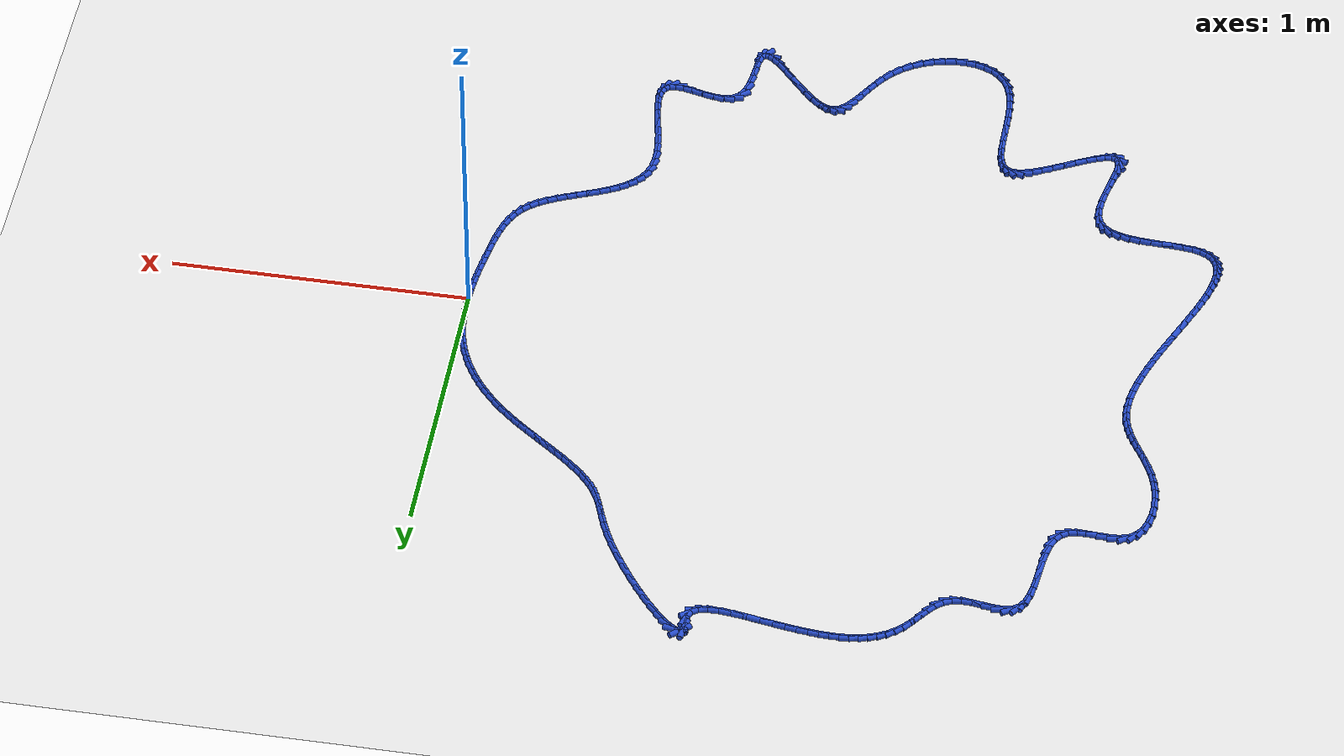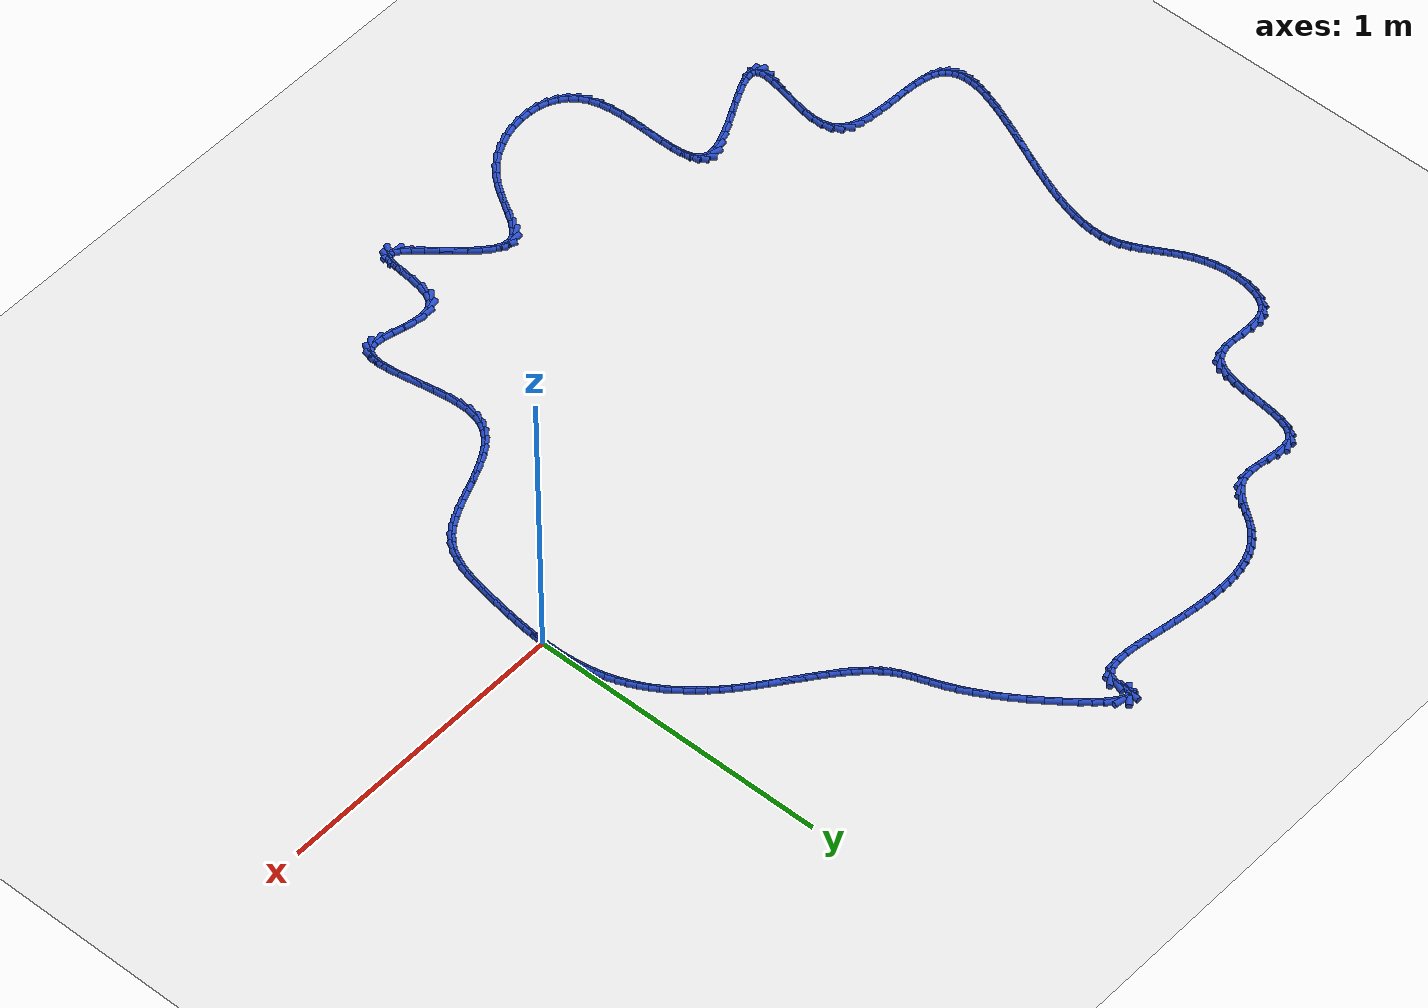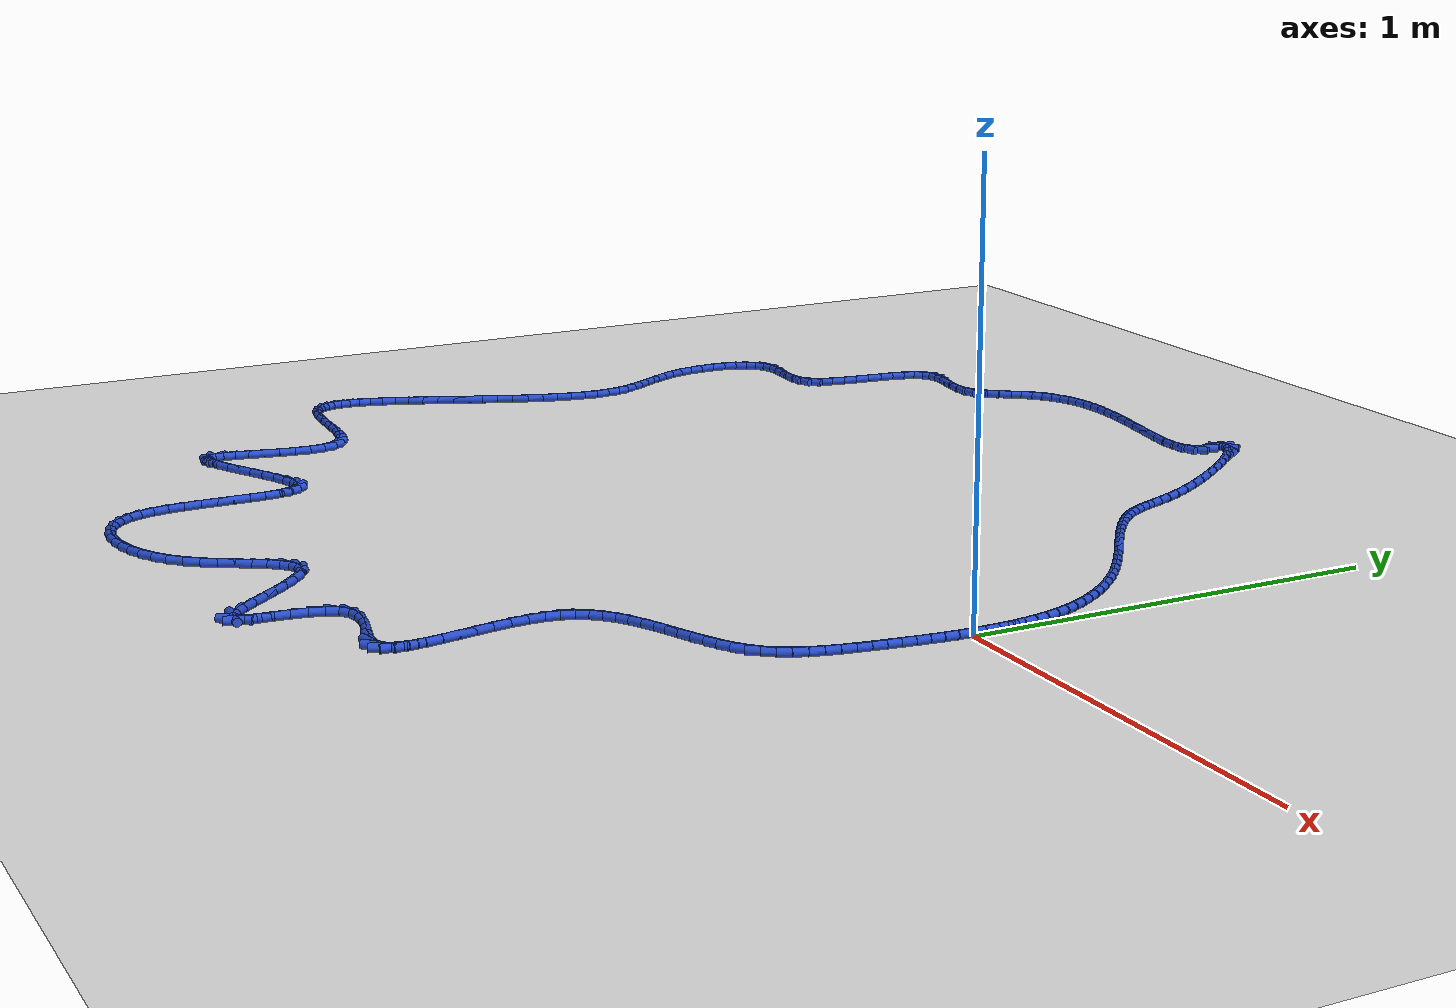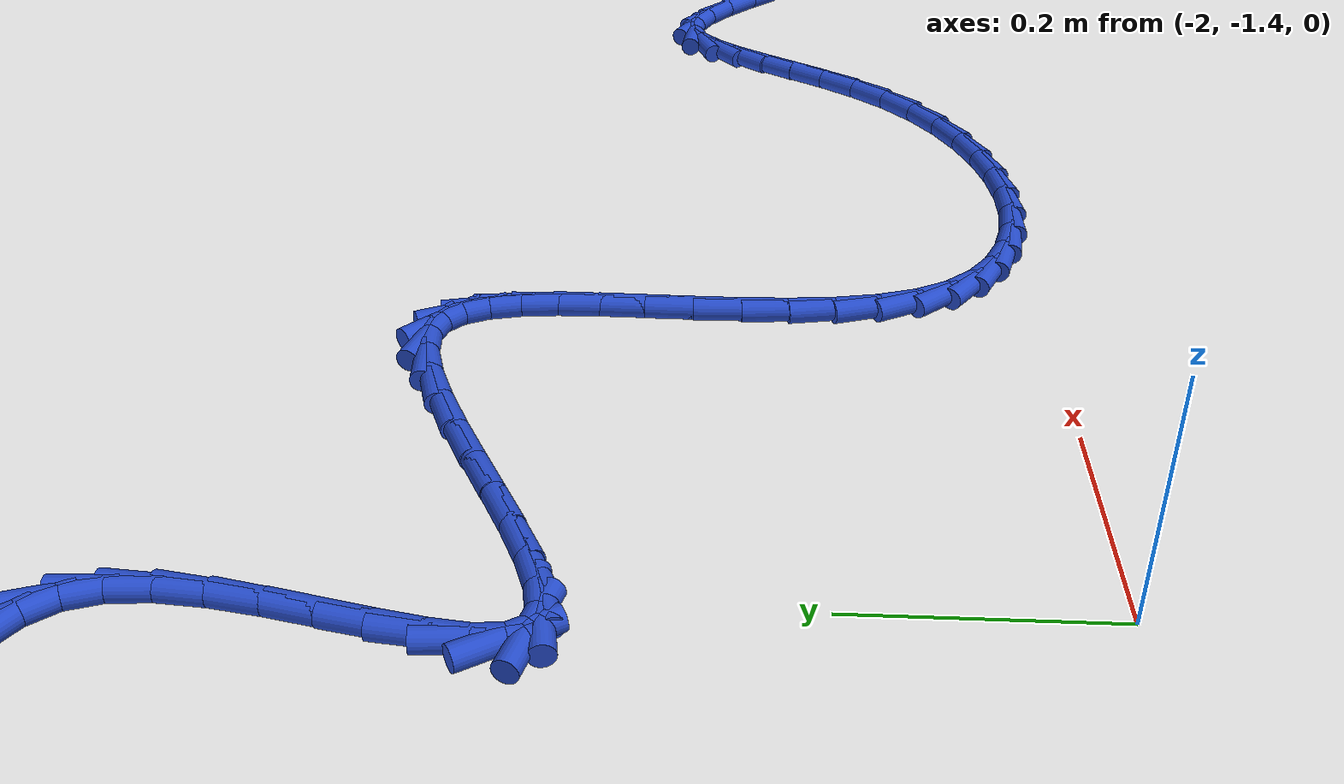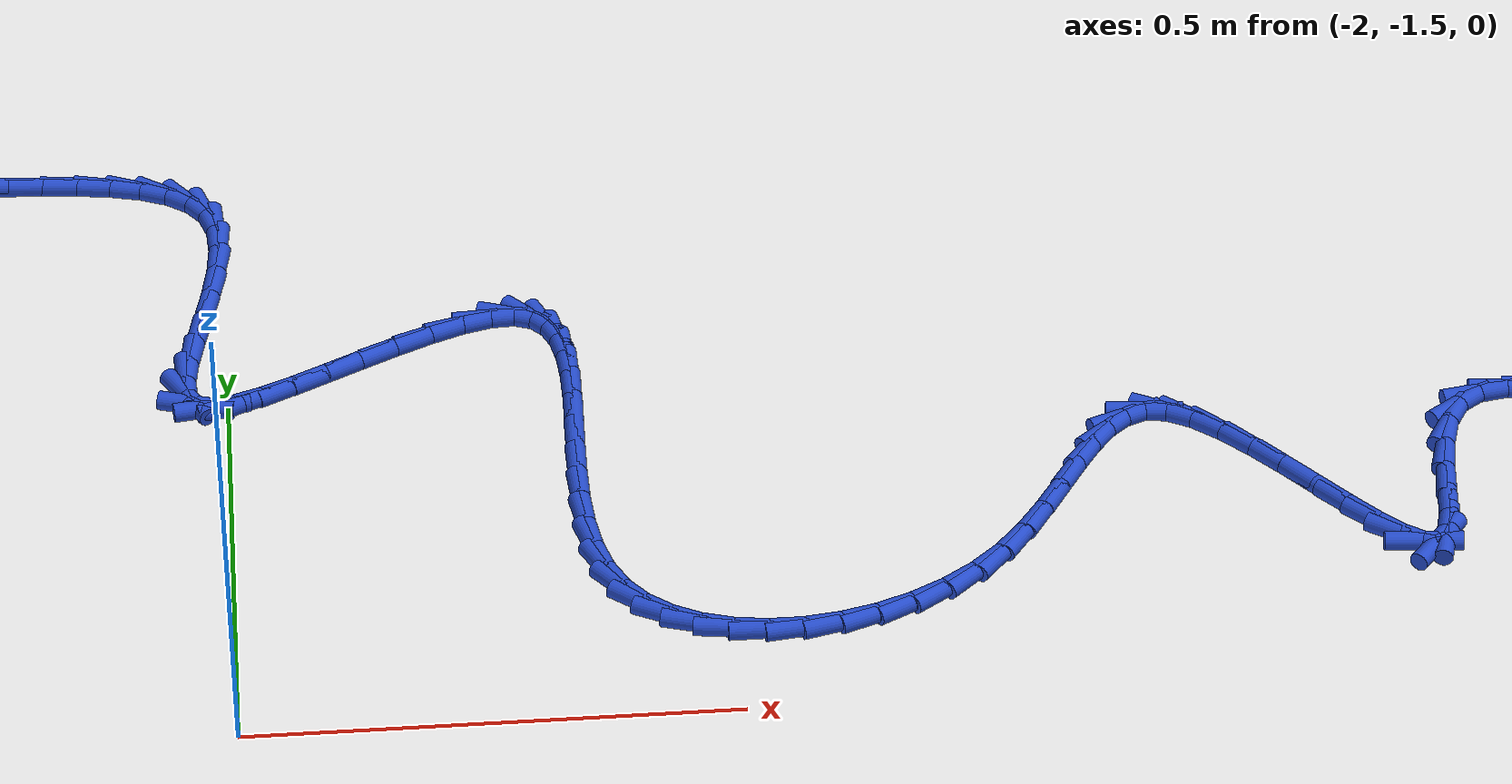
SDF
<sdf version="1.6">
 <world name="default">
  <light name="sun" type="directional">
   <pose>0 0 10 0 -0 0</pose>
   <diffuse>0.8 0.8 0.8 1</diffuse>
   <specular>0.2 0.2 0.2 1</specular>
   <attenuation>
    <range>1000</range>
    <constant>0.9</constant>
    <linear>0.01</linear>
    <quadratic>0.001</quadratic>
   </attenuation>
   <direction>-0.5 0.1 -0.9</direction>
  </light>
  <model name="ground_plane">
   <static>1</static>
   <link name="link">
    <collision name="collision">
     <geometry><plane><normal>0 0 1</normal><size>100 100</size></plane></geometry>
     <surface><friction><ode><mu>100</mu><mu2>50</mu2></ode></friction></surface>
    </collision>
    <visual name="visual">
     <cast_shadows>0</cast_shadows>
     <geometry><plane><normal>0 0 1</normal><size>100 100</size></plane></geometry>
     <material>
      <script><uri>file://media/materials/scripts/gazebo.material</uri><name>Gazebo/WhiteGlow</name></script>
     </material>
    </visual>
   </link>
  </model>
  <gravity>0 0 -9.8</gravity>
  <magnetic_field>6e-06 2.3e-05 -4.2e-05</magnetic_field>
  <atmosphere type="adiabatic"/>
  <physics name="default_physics" default="0" type="ode">
   <max_step_size>0.001</max_step_size>
   <real_time_factor>1</real_time_factor>
   <real_time_update_rate>1000</real_time_update_rate>
  </physics>
  <scene><ambient>0.4 0.4 0.4 1</ambient><background>0.7 0.7 0.7 1</background><shadows>1</shadows></scene>
  <spherical_coordinates>
   <surface_model>EARTH_WGS84</surface_model>
   <latitude_deg>0</latitude_deg>
   <longitude_deg>0</longitude_deg>
   <elevation>0</elevation>
   <heading_deg>0</heading_deg>
  </spherical_coordinates>
  <model name="line">
   <link name="link_0">
    <pose>8.239936510889834e-18 -6.245004513516506e-17 0.01 0 1.57 1.556347999024885</pose>
    <collision name="collision">
     <geometry><cylinder><radius>0.01</radius><length>0.08</length></cylinder></geometry>
    </collision>
    <visual name="visual">
     <material>
      <script><name>Gazebo/Blue</name><uri>file://media/materials/scripts/gazebo.material</uri></script>
     </material>
     <geometry><cylinder><radius>0.01</radius><length>0.08</length></cylinder></geometry>
    </visual>
   </link>
   <link name="link_1">
    <pose>0.00046270269200625146 0.03202242514727677 0.01 0 1.57 -1.5501684178101491</pose>
    <collision name="collision">
     <geometry><cylinder><radius>0.01</radius><length>0.08</length></cylinder></geometry>
    </collision>
    <visual name="visual">
     <material>
      <script><name>Gazebo/Blue</name><uri>file://media/materials/scripts/gazebo.material</uri></script>
     </material>
     <geometry><cylinder><radius>0.01</radius><length>0.08</length></cylinder></geometry>
    </visual>
   </link>
   <link name="link_2">
    <pose>-0.00020141020750565265 0.0642127310881978 0.01 0 1.57 -1.511176370956596</pose>
    <collision name="collision">
     <geometry><cylinder><radius>0.01</radius><length>0.08</length></cylinder></geometry>
    </collision>
    <visual name="visual">
     <material>
      <script><name>Gazebo/Blue</name><uri>file://media/materials/scripts/gazebo.material</uri></script>
     </material>
     <geometry><cylinder><radius>0.01</radius><length>0.08</length></cylinder></geometry>
    </visual>
   </link>
   <link name="link_3">
    <pose>-0.0021238337516538714 0.09641914923511406 0.01 0 1.57 -1.4678824195072182</pose>
    <collision name="collision">
     <geometry><cylinder><radius>0.01</radius><length>0.08</length></cylinder></geometry>
    </collision>
    <visual name="visual">
     <material>
      <script><name>Gazebo/Blue</name><uri>file://media/materials/scripts/gazebo.material</uri></script>
     </material>
     <geometry><cylinder><radius>0.01</radius><length>0.08</length></cylinder></geometry>
    </visual>
   </link>
   <link name="link_4">
    <pose>-0.005436062993556576 0.12848991100037652 0.01 0 1.57 -1.4198752287430998</pose>
    <collision name="collision">
     <geometry><cylinder><radius>0.01</radius><length>0.08</length></cylinder></geometry>
    </collision>
    <visual name="visual">
     <material>
      <script><name>Gazebo/Blue</name><uri>file://media/materials/scripts/gazebo.material</uri></script>
     </material>
     <geometry><cylinder><radius>0.01</radius><length>0.08</length></cylinder></geometry>
    </visual>
   </link>
   <link name="link_5">
    <pose>-0.010269592986331934 0.16027324779633612 0.01 0 1.57 -1.3667376374764861</pose>
    <collision name="collision">
     <geometry><cylinder><radius>0.01</radius><length>0.08</length></cylinder></geometry>
    </collision>
    <visual name="visual">
     <material>
      <script><name>Gazebo/Blue</name><uri>file://media/materials/scripts/gazebo.material</uri></script>
     </material>
     <geometry><cylinder><radius>0.01</radius><length>0.08</length></cylinder></geometry>
    </visual>
   </link>
   <link name="link_6">
    <pose>-0.01675591878309812 0.191617391035344 0.01 0 1.57 -1.3080770948034395</pose>
    <collision name="collision">
     <geometry><cylinder><radius>0.01</radius><length>0.08</length></cylinder></geometry>
    </collision>
    <visual name="visual">
     <material>
      <script><name>Gazebo/Blue</name><uri>file://media/materials/scripts/gazebo.material</uri></script>
     </material>
     <geometry><cylinder><radius>0.01</radius><length>0.08</length></cylinder></geometry>
    </visual>
   </link>
   <link name="link_7">
    <pose>-0.02502653543697329 0.22237057212975092 0.01 0 1.57 -1.244849307218012</pose>
    <collision name="collision">
     <geometry><cylinder><radius>0.01</radius><length>0.08</length></cylinder></geometry>
    </collision>
    <visual name="visual">
     <material>
      <script><name>Gazebo/Blue</name><uri>file://media/materials/scripts/gazebo.material</uri></script>
     </material>
     <geometry><cylinder><radius>0.01</radius><length>0.08</length></cylinder></geometry>
    </visual>
   </link>
   <link name="link_8">
    <pose>-0.03517862759599899 0.25240611391993895 0.01 0 1.57 -1.1822459592128365</pose>
    <collision name="collision">
     <geometry><cylinder><radius>0.01</radius><length>0.08</length></cylinder></geometry>
    </collision>
    <visual name="visual">
     <material>
      <script><name>Gazebo/Blue</name><uri>file://media/materials/scripts/gazebo.material</uri></script>
     </material>
     <geometry><cylinder><radius>0.01</radius><length>0.08</length></cylinder></geometry>
    </visual>
   </link>
   <link name="link_9">
    <pose>-0.04717008699567996 0.28169920508209995 0.01 0 1.57 -1.1218946879295684</pose>
    <collision name="collision">
     <geometry><cylinder><radius>0.01</radius><length>0.08</length></cylinder></geometry>
    </collision>
    <visual name="visual">
     <material>
      <script><name>Gazebo/Blue</name><uri>file://media/materials/scripts/gazebo.material</uri></script>
     </material>
     <geometry><cylinder><radius>0.01</radius><length>0.08</length></cylinder></geometry>
    </visual>
   </link>
   <link name="link_10">
    <pose>-0.060923461678623315 0.3102508813707308 0.01 0 1.57 -1.064051859200754</pose>
    <collision name="collision">
     <geometry><cylinder><radius>0.01</radius><length>0.08</length></cylinder></geometry>
    </collision>
    <visual name="visual">
     <material>
      <script><name>Gazebo/Blue</name><uri>file://media/materials/scripts/gazebo.material</uri></script>
     </material>
     <geometry><cylinder><radius>0.01</radius><length>0.08</length></cylinder></geometry>
    </visual>
   </link>
   <link name="link_11">
    <pose>-0.07636129968322446 0.33806217854340825 0.01 0 1.57 -1.0088867973929567</pose>
    <collision name="collision">
     <geometry><cylinder><radius>0.01</radius><length>0.08</length></cylinder></geometry>
    </collision>
    <visual name="visual">
     <material>
      <script><name>Gazebo/Blue</name><uri>file://media/materials/scripts/gazebo.material</uri></script>
     </material>
     <geometry><cylinder><radius>0.01</radius><length>0.08</length></cylinder></geometry>
    </visual>
   </link>
   <link name="link_12">
    <pose>-0.09340614904787883 0.36513413235770925 0.01 0 1.57 -0.9564895008531517</pose>
    <collision name="collision">
     <geometry><cylinder><radius>0.01</radius><length>0.08</length></cylinder></geometry>
    </collision>
    <visual name="visual">
     <material>
      <script><name>Gazebo/Blue</name><uri>file://media/materials/scripts/gazebo.material</uri></script>
     </material>
     <geometry><cylinder><radius>0.01</radius><length>0.08</length></cylinder></geometry>
    </visual>
   </link>
   <link name="link_13">
    <pose>-0.11198055781098185 0.3914677785712104 0.01 0 1.57 -0.9068817135548961</pose>
    <collision name="collision">
     <geometry><cylinder><radius>0.01</radius><length>0.08</length></cylinder></geometry>
    </collision>
    <visual name="visual">
     <material>
      <script><name>Gazebo/Blue</name><uri>file://media/materials/scripts/gazebo.material</uri></script>
     </material>
     <geometry><cylinder><radius>0.01</radius><length>0.08</length></cylinder></geometry>
    </visual>
   </link>
   <link name="link_14">
    <pose>-0.13200707401092895 0.41706415294148874 0.01 0 1.57 -0.8600294756403803</pose>
    <collision name="collision">
     <geometry><cylinder><radius>0.01</radius><length>0.08</length></cylinder></geometry>
    </collision>
    <visual name="visual">
     <material>
      <script><name>Gazebo/Blue</name><uri>file://media/materials/scripts/gazebo.material</uri></script>
     </material>
     <geometry><cylinder><radius>0.01</radius><length>0.08</length></cylinder></geometry>
    </visual>
   </link>
   <link name="link_15">
    <pose>-0.1534082456861156 0.441924291226121 0.01 0 1.57 -0.8158556753269327</pose>
    <collision name="collision">
     <geometry><cylinder><radius>0.01</radius><length>0.08</length></cylinder></geometry>
    </collision>
    <visual name="visual">
     <material>
      <script><name>Gazebo/Blue</name><uri>file://media/materials/scripts/gazebo.material</uri></script>
     </material>
     <geometry><cylinder><radius>0.01</radius><length>0.08</length></cylinder></geometry>
    </visual>
   </link>
   <link name="link_16">
    <pose>-0.17610662087493728 0.46604922918268404 0.01 0 1.57 -0.7742516029679208</pose>
    <collision name="collision">
     <geometry><cylinder><radius>0.01</radius><length>0.08</length></cylinder></geometry>
    </collision>
    <visual name="visual">
     <material>
      <script><name>Gazebo/Blue</name><uri>file://media/materials/scripts/gazebo.material</uri></script>
     </material>
     <geometry><cylinder><radius>0.01</radius><length>0.08</length></cylinder></geometry>
    </visual>
   </link>
   <link name="link_17">
    <pose>-0.20002474761578937 0.48944000256875453 0.01 0 1.57 -0.7352273542439206</pose>
    <collision name="collision">
     <geometry><cylinder><radius>0.01</radius><length>0.08</length></cylinder></geometry>
    </collision>
    <visual name="visual">
     <material>
      <script><name>Gazebo/Blue</name><uri>file://media/materials/scripts/gazebo.material</uri></script>
     </material>
     <geometry><cylinder><radius>0.01</radius><length>0.08</length></cylinder></geometry>
    </visual>
   </link>
   <link name="link_18">
    <pose>-0.22508090842203893 0.5121001851655561 0.01 0 1.57 -0.7014949021345893</pose>
    <collision name="collision">
     <geometry><cylinder><radius>0.01</radius><length>0.08</length></cylinder></geometry>
    </collision>
    <visual name="visual">
     <material>
      <script><name>Gazebo/Blue</name><uri>file://media/materials/scripts/gazebo.material</uri></script>
     </material>
     <geometry><cylinder><radius>0.01</radius><length>0.08</length></cylinder></geometry>
    </visual>
   </link>
   <link name="link_19">
    <pose>-0.25110456837943995 0.5340861978786378 0.01 0 1.57 -0.675398933111013</pose>
    <collision name="collision">
     <geometry><cylinder><radius>0.01</radius><length>0.08</length></cylinder></geometry>
    </collision>
    <visual name="visual">
     <material>
      <script><name>Gazebo/Blue</name><uri>file://media/materials/scripts/gazebo.material</uri></script>
     </material>
     <geometry><cylinder><radius>0.01</radius><length>0.08</length></cylinder></geometry>
    </visual>
   </link>
   <link name="link_20">
    <pose>-0.27784124863584436 0.555504408970076 0.01 0 1.57 -0.656662161814817</pose>
    <collision name="collision">
     <geometry><cylinder><radius>0.01</radius><length>0.08</length></cylinder></geometry>
    </collision>
    <visual name="visual">
     <material>
      <script><name>Gazebo/Blue</name><uri>file://media/materials/scripts/gazebo.material</uri></script>
     </material>
     <geometry><cylinder><radius>0.01</radius><length>0.08</length></cylinder></geometry>
    </visual>
   </link>
   <link name="link_21">
    <pose>-0.3050331804852227 0.5764631441929683 0.01 0 1.57 -0.6450304318351904</pose>
    <collision name="collision">
     <geometry><cylinder><radius>0.01</radius><length>0.08</length></cylinder></geometry>
    </collision>
    <visual name="visual">
     <material>
      <script><name>Gazebo/Blue</name><uri>file://media/materials/scripts/gazebo.material</uri></script>
     </material>
     <geometry><cylinder><radius>0.01</radius><length>0.08</length></cylinder></geometry>
    </visual>
   </link>
   <link name="link_22">
    <pose>-0.33242259522154577 0.5970707293004115 0.01 0 1.57 -0.6404007062076207</pose>
    <collision name="collision">
     <geometry><cylinder><radius>0.01</radius><length>0.08</length></cylinder></geometry>
    </collision>
    <visual name="visual">
     <material>
      <script><name>Gazebo/Blue</name><uri>file://media/materials/scripts/gazebo.material</uri></script>
     </material>
     <geometry><cylinder><radius>0.01</radius><length>0.08</length></cylinder></geometry>
    </visual>
   </link>
   <link name="link_23">
    <pose>-0.3597517241387842 0.617435490045503 0.01 0 1.57 -0.6428363115628816</pose>
    <collision name="collision">
     <geometry><cylinder><radius>0.01</radius><length>0.08</length></cylinder></geometry>
    </collision>
    <visual name="visual">
     <material>
      <script><name>Gazebo/Blue</name><uri>file://media/materials/scripts/gazebo.material</uri></script>
     </material>
     <geometry><cylinder><radius>0.01</radius><length>0.08</length></cylinder></geometry>
    </visual>
   </link>
   <link name="link_24">
    <pose>-0.38676279853090895 0.6376657521813405 0.01 0 1.57 -0.6525815560505088</pose>
    <collision name="collision">
     <geometry><cylinder><radius>0.01</radius><length>0.08</length></cylinder></geometry>
    </collision>
    <visual name="visual">
     <material>
      <script><name>Gazebo/Blue</name><uri>file://media/materials/scripts/gazebo.material</uri></script>
     </material>
     <geometry><cylinder><radius>0.01</radius><length>0.08</length></cylinder></geometry>
    </visual>
   </link>
   <link name="link_25">
    <pose>-0.4131980496918904 0.6578698414610208 0.01 0 1.57 -0.6700772859273006</pose>
    <collision name="collision">
     <geometry><cylinder><radius>0.01</radius><length>0.08</length></cylinder></geometry>
    </collision>
    <visual name="visual">
     <material>
      <script><name>Gazebo/Blue</name><uri>file://media/materials/scripts/gazebo.material</uri></script>
     </material>
     <geometry><cylinder><radius>0.01</radius><length>0.08</length></cylinder></geometry>
    </visual>
   </link>
   <link name="link_26">
    <pose>-0.4387997089156994 0.6781560836376413 0.01 0 1.57 -0.6959763503585942</pose>
    <collision name="collision">
     <geometry><cylinder><radius>0.01</radius><length>0.08</length></cylinder></geometry>
    </collision>
    <visual name="visual">
     <material>
      <script><name>Gazebo/Blue</name><uri>file://media/materials/scripts/gazebo.material</uri></script>
     </material>
     <geometry><cylinder><radius>0.01</radius><length>0.08</length></cylinder></geometry>
    </visual>
   </link>
   <link name="link_27">
    <pose>-0.4633100074963067 0.6986328044642993 0.01 0 1.57 -0.7311541261599552</pose>
    <collision name="collision">
     <geometry><cylinder><radius>0.01</radius><length>0.08</length></cylinder></geometry>
    </collision>
    <visual name="visual">
     <material>
      <script><name>Gazebo/Blue</name><uri>file://media/materials/scripts/gazebo.material</uri></script>
     </material>
     <geometry><cylinder><radius>0.01</radius><length>0.08</length></cylinder></geometry>
    </visual>
   </link>
   <link name="link_28">
    <pose>-0.48647117672768303 0.7194083296940923 0.01 0 1.57 -0.7767029563622707</pose>
    <collision name="collision">
     <geometry><cylinder><radius>0.01</radius><length>0.08</length></cylinder></geometry>
    </collision>
    <visual name="visual">
     <material>
      <script><name>Gazebo/Blue</name><uri>file://media/materials/scripts/gazebo.material</uri></script>
     </material>
     <geometry><cylinder><radius>0.01</radius><length>0.08</length></cylinder></geometry>
    </visual>
   </link>
   <link name="link_29">
    <pose>-0.5080254479037991 0.7405909850801176 0.01 0 1.57 -0.8338891792913433</pose>
    <collision name="collision">
     <geometry><cylinder><radius>0.01</radius><length>0.08</length></cylinder></geometry>
    </collision>
    <visual name="visual">
     <material>
      <script><name>Gazebo/Blue</name><uri>file://media/materials/scripts/gazebo.material</uri></script>
     </material>
     <geometry><cylinder><radius>0.01</radius><length>0.08</length></cylinder></geometry>
    </visual>
   </link>
   <link name="link_30">
    <pose>-0.5277150523186256 0.762289096375472 0.01 0 1.57 -0.9040370818781435</pose>
    <collision name="collision">
     <geometry><cylinder><radius>0.01</radius><length>0.08</length></cylinder></geometry>
    </collision>
    <visual name="visual">
     <material>
      <script><name>Gazebo/Blue</name><uri>file://media/materials/scripts/gazebo.material</uri></script>
     </material>
     <geometry><cylinder><radius>0.01</radius><length>0.08</length></cylinder></geometry>
    </visual>
   </link>
   <link name="link_31">
    <pose>-0.5452822212661331 0.784610989333253 0.01 0 1.57 -0.9882902400405796</pose>
    <collision name="collision">
     <geometry><cylinder><radius>0.01</radius><length>0.08</length></cylinder></geometry>
    </collision>
    <visual name="visual">
     <material>
      <script><name>Gazebo/Blue</name><uri>file://media/materials/scripts/gazebo.material</uri></script>
     </material>
     <geometry><cylinder><radius>0.01</radius><length>0.08</length></cylinder></geometry>
    </visual>
   </link>
   <link name="link_32">
    <pose>-0.5604691860402927 0.8076649897065584 0.01 0 1.57 -1.0823117957941057</pose>
    <collision name="collision">
     <geometry><cylinder><radius>0.01</radius><length>0.08</length></cylinder></geometry>
    </collision>
    <visual name="visual">
     <material>
      <script><name>Gazebo/Blue</name><uri>file://media/materials/scripts/gazebo.material</uri></script>
     </material>
     <geometry><cylinder><radius>0.01</radius><length>0.08</length></cylinder></geometry>
    </visual>
   </link>
   <link name="link_33">
    <pose>-0.5731873946283736 0.8315964486987707 0.01 0 1.57 -1.1576529503989859</pose>
    <collision name="collision">
     <geometry><cylinder><radius>0.01</radius><length>0.08</length></cylinder></geometry>
    </collision>
    <visual name="visual">
     <material>
      <script><name>Gazebo/Blue</name><uri>file://media/materials/scripts/gazebo.material</uri></script>
     </material>
     <geometry><cylinder><radius>0.01</radius><length>0.08</length></cylinder></geometry>
    </visual>
   </link>
   <link name="link_34">
    <pose>-0.5842092679235866 0.8567391026477709 0.01 0 1.57 -1.200900658465214</pose>
    <collision name="collision">
     <geometry><cylinder><radius>0.01</radius><length>0.08</length></cylinder></geometry>
    </collision>
    <visual name="visual">
     <material>
      <script><name>Gazebo/Blue</name><uri>file://media/materials/scripts/gazebo.material</uri></script>
     </material>
     <geometry><cylinder><radius>0.01</radius><length>0.08</length></cylinder></geometry>
    </visual>
   </link>
   <link name="link_35">
    <pose>-0.5945803694636427 0.8834864528543862 0.01 0 1.57 -1.212440061428917</pose>
    <collision name="collision">
     <geometry><cylinder><radius>0.01</radius><length>0.08</length></cylinder></geometry>
    </collision>
    <visual name="visual">
     <material>
      <script><name>Gazebo/Blue</name><uri>file://media/materials/scripts/gazebo.material</uri></script>
     </material>
     <geometry><cylinder><radius>0.01</radius><length>0.08</length></cylinder></geometry>
    </visual>
   </link>
   <link name="link_36">
    <pose>-0.6053463736047532 0.91223202486708 0.01 0 1.57 -1.1971845372921317</pose>
    <collision name="collision">
     <geometry><cylinder><radius>0.01</radius><length>0.08</length></cylinder></geometry>
    </collision>
    <visual name="visual">
     <material>
      <script><name>Gazebo/Blue</name><uri>file://media/materials/scripts/gazebo.material</uri></script>
     </material>
     <geometry><cylinder><radius>0.01</radius><length>0.08</length></cylinder></geometry>
    </visual>
   </link>
   <link name="link_37">
    <pose>-0.6175529547031305 0.9433693442343164 0.01 0 1.57 -1.1620611873588562</pose>
    <collision name="collision">
     <geometry><cylinder><radius>0.01</radius><length>0.08</length></cylinder></geometry>
    </collision>
    <visual name="visual">
     <material>
      <script><name>Gazebo/Blue</name><uri>file://media/materials/scripts/gazebo.material</uri></script>
     </material>
     <geometry><cylinder><radius>0.01</radius><length>0.08</length></cylinder></geometry>
    </visual>
   </link>
   <link name="link_38">
    <pose>-0.6322457871149865 0.9772919365045591 0.01 0 1.57 -1.1142273092928259</pose>
    <collision name="collision">
     <geometry><cylinder><radius>0.01</radius><length>0.08</length></cylinder></geometry>
    </collision>
    <visual name="visual">
     <material>
      <script><name>Gazebo/Blue</name><uri>file://media/materials/scripts/gazebo.material</uri></script>
     </material>
     <geometry><cylinder><radius>0.01</radius><length>0.08</length></cylinder></geometry>
    </visual>
   </link>
   <link name="link_39">
    <pose>-0.6504684769099253 1.0143915439300093 0.01 0 1.57 -1.0650984541148942</pose>
    <collision name="collision">
     <geometry><cylinder><radius>0.01</radius><length>0.08</length></cylinder></geometry>
    </collision>
    <visual name="visual">
     <material>
      <script><name>Gazebo/Blue</name><uri>file://media/materials/scripts/gazebo.material</uri></script>
     </material>
     <geometry><cylinder><radius>0.01</radius><length>0.08</length></cylinder></geometry>
    </visual>
   </link>
   <link name="link_40">
    <pose>-0.6727343675329157 1.0546027113158039 0.01 0 1.57 -1.0256233409169349</pose>
    <collision name="collision">
     <geometry><cylinder><radius>0.01</radius><length>0.08</length></cylinder></geometry>
    </collision>
    <visual name="visual">
     <material>
      <script><name>Gazebo/Blue</name><uri>file://media/materials/scripts/gazebo.material</uri></script>
     </material>
     <geometry><cylinder><radius>0.01</radius><length>0.08</length></cylinder></geometry>
    </visual>
   </link>
   <link name="link_41">
    <pose>-0.698325107132864 1.0967980041406897 0.01 0 1.57 -0.9921833954823563</pose>
    <collision name="collision">
     <geometry><cylinder><radius>0.01</radius><length>0.08</length></cylinder></geometry>
    </collision>
    <visual name="visual">
     <material>
      <script><name>Gazebo/Blue</name><uri>file://media/materials/scripts/gazebo.material</uri></script>
     </material>
     <geometry><cylinder><radius>0.01</radius><length>0.08</length></cylinder></geometry>
    </visual>
   </link>
   <link name="link_42">
    <pose>-0.7263478838506358 1.1396995668154652 0.01 0 1.57 -0.9611649062504479</pose>
    <collision name="collision">
     <geometry><cylinder><radius>0.01</radius><length>0.08</length></cylinder></geometry>
    </collision>
    <visual name="visual">
     <material>
      <script><name>Gazebo/Blue</name><uri>file://media/materials/scripts/gazebo.material</uri></script>
     </material>
     <geometry><cylinder><radius>0.01</radius><length>0.08</length></cylinder></geometry>
    </visual>
   </link>
   <link name="link_43">
    <pose>-0.755909885827098 1.182029543750929 0.01 0 1.57 -0.9297024657896009</pose>
    <collision name="collision">
     <geometry><cylinder><radius>0.01</radius><length>0.08</length></cylinder></geometry>
    </collision>
    <visual name="visual">
     <material>
      <script><name>Gazebo/Blue</name><uri>file://media/materials/scripts/gazebo.material</uri></script>
     </material>
     <geometry><cylinder><radius>0.01</radius><length>0.08</length></cylinder></geometry>
    </visual>
   </link>
   <link name="link_44">
    <pose>-0.7861183012031175 1.2225100793578816 0.01 0 1.57 -0.8947601753995672</pose>
    <collision name="collision">
     <geometry><cylinder><radius>0.01</radius><length>0.08</length></cylinder></geometry>
    </collision>
    <visual name="visual">
     <material>
      <script><name>Gazebo/Blue</name><uri>file://media/materials/scripts/gazebo.material</uri></script>
     </material>
     <geometry><cylinder><radius>0.01</radius><length>0.08</length></cylinder></geometry>
    </visual>
   </link>
   <link name="link_45">
    <pose>-0.8160803181195608 1.2598633180471206 0.01 0 1.57 -0.8520826936787014</pose>
    <collision name="collision">
     <geometry><cylinder><radius>0.01</radius><length>0.08</length></cylinder></geometry>
    </collision>
    <visual name="visual">
     <material>
      <script><name>Gazebo/Blue</name><uri>file://media/materials/scripts/gazebo.material</uri></script>
     </material>
     <geometry><cylinder><radius>0.01</radius><length>0.08</length></cylinder></geometry>
    </visual>
   </link>
   <link name="link_46">
    <pose>-0.8449031247172947 1.2928114042294456 0.01 0 1.57 -0.7941720775234102</pose>
    <collision name="collision">
     <geometry><cylinder><radius>0.01</radius><length>0.08</length></cylinder></geometry>
    </collision>
    <visual name="visual">
     <material>
      <script><name>Gazebo/Blue</name><uri>file://media/materials/scripts/gazebo.material</uri></script>
     </material>
     <geometry><cylinder><radius>0.01</radius><length>0.08</length></cylinder></geometry>
    </visual>
   </link>
   <link name="link_47">
    <pose>-0.8716939091371854 1.3200764823156557 0.01 0 1.57 -0.7049355665056798</pose>
    <collision name="collision">
     <geometry><cylinder><radius>0.01</radius><length>0.08</length></cylinder></geometry>
    </collision>
    <visual name="visual">
     <material>
      <script><name>Gazebo/Blue</name><uri>file://media/materials/scripts/gazebo.material</uri></script>
     </material>
     <geometry><cylinder><radius>0.01</radius><length>0.08</length></cylinder></geometry>
    </visual>
   </link>
   <link name="link_48">
    <pose>-0.8955598595201004 1.3403806967165504 0.01 0 1.57 -0.5417575589643765</pose>
    <collision name="collision">
     <geometry><cylinder><radius>0.01</radius><length>0.08</length></cylinder></geometry>
    </collision>
    <visual name="visual">
     <material>
      <script><name>Gazebo/Blue</name><uri>file://media/materials/scripts/gazebo.material</uri></script>
     </material>
     <geometry><cylinder><radius>0.01</radius><length>0.08</length></cylinder></geometry>
    </visual>
   </link>
   <link name="link_49">
    <pose>-0.9156081640069054 1.3524461918429276 0.01 0 1.57 -0.1646800051082283</pose>
    <collision name="collision">
     <geometry><cylinder><radius>0.01</radius><length>0.08</length></cylinder></geometry>
    </collision>
    <visual name="visual">
     <material>
      <script><name>Gazebo/Blue</name><uri>file://media/materials/scripts/gazebo.material</uri></script>
     </material>
     <geometry><cylinder><radius>0.01</radius><length>0.08</length></cylinder></geometry>
    </visual>
   </link>
   <link name="link_50">
    <pose>-0.930946010738468 1.3549951121055879 0.01 0 1.57 0.702769171397926</pose>
    <collision name="collision">
     <geometry><cylinder><radius>0.01</radius><length>0.08</length></cylinder></geometry>
    </collision>
    <visual name="visual">
     <material>
      <script><name>Gazebo/Blue</name><uri>file://media/materials/scripts/gazebo.material</uri></script>
     </material>
     <geometry><cylinder><radius>0.01</radius><length>0.08</length></cylinder></geometry>
    </visual>
   </link>
   <link name="link_51">
    <pose>-0.9406805878556543 1.3467496019153293 0.01 0 1.57 1.41273387409286</pose>
    <collision name="collision">
     <geometry><cylinder><radius>0.01</radius><length>0.08</length></cylinder></geometry>
    </collision>
    <visual name="visual">
     <material>
      <script><name>Gazebo/Blue</name><uri>file://media/materials/scripts/gazebo.material</uri></script>
     </material>
     <geometry><cylinder><radius>0.01</radius><length>0.08</length></cylinder></geometry>
    </visual>
   </link>
   <link name="link_52">
    <pose>-0.9439190834993308 1.3264318056829507 0.01 0 1.57 -1.5221675186880352</pose>
    <collision name="collision">
     <geometry><cylinder><radius>0.01</radius><length>0.08</length></cylinder></geometry>
    </collision>
    <visual name="visual">
     <material>
      <script><name>Gazebo/Blue</name><uri>file://media/materials/scripts/gazebo.material</uri></script>
     </material>
     <geometry><cylinder><radius>0.01</radius><length>0.08</length></cylinder></geometry>
    </visual>
   </link>
   <link name="link_53">
    <pose>-0.9424291690063107 1.2958174448702005 0.01 0 1.57 1.2154205038277377</pose>
    <collision name="collision">
     <geometry><cylinder><radius>0.01</radius><length>0.08</length></cylinder></geometry>
    </collision>
    <visual name="visual">
     <material>
      <script><name>Gazebo/Blue</name><uri>file://media/materials/scripts/gazebo.material</uri></script>
     </material>
     <geometry><cylinder><radius>0.01</radius><length>0.08</length></cylinder></geometry>
    </visual>
   </link>
   <link name="link_54">
    <pose>-0.951201153349756 1.2721817337904735 0.01 0 1.57 0.6095122051540365</pose>
    <collision name="collision">
     <geometry><cylinder><radius>0.01</radius><length>0.08</length></cylinder></geometry>
    </collision>
    <visual name="visual">
     <material>
      <script><name>Gazebo/Blue</name><uri>file://media/materials/scripts/gazebo.material</uri></script>
     </material>
     <geometry><cylinder><radius>0.01</radius><length>0.08</length></cylinder></geometry>
    </visual>
   </link>
   <link name="link_55">
    <pose>-0.9716135039518669 1.2579299728107183 0.01 0 1.57 0.21533407115697037</pose>
    <collision name="collision">
     <geometry><cylinder><radius>0.01</radius><length>0.08</length></cylinder></geometry>
    </collision>
    <visual name="visual">
     <material>
      <script><name>Gazebo/Blue</name><uri>file://media/materials/scripts/gazebo.material</uri></script>
     </material>
     <geometry><cylinder><radius>0.01</radius><length>0.08</length></cylinder></geometry>
    </visual>
   </link>
   <link name="link_56">
    <pose>-1.0014193933348703 1.2514106724744487 0.01 0 1.57 0.011861373339010307</pose>
    <collision name="collision">
     <geometry><cylinder><radius>0.01</radius><length>0.08</length></cylinder></geometry>
    </collision>
    <visual name="visual">
     <material>
      <script><name>Gazebo/Blue</name><uri>file://media/materials/scripts/gazebo.material</uri></script>
     </material>
     <geometry><cylinder><radius>0.01</radius><length>0.08</length></cylinder></geometry>
    </visual>
   </link>
   <link name="link_57">
    <pose>-1.0383719940209934 1.2509723433251763 0.01 0 1.57 -0.09507487366044656</pose>
    <collision name="collision">
     <geometry><cylinder><radius>0.01</radius><length>0.08</length></cylinder></geometry>
    </collision>
    <visual name="visual">
     <material>
      <script><name>Gazebo/Blue</name><uri>file://media/materials/scripts/gazebo.material</uri></script>
     </material>
     <geometry><cylinder><radius>0.01</radius><length>0.08</length></cylinder></geometry>
    </visual>
   </link>
   <link name="link_58">
    <pose>-1.0802244785324633 1.2549634959064135 0.01 0 1.57 -0.150939853694309</pose>
    <collision name="collision">
     <geometry><cylinder><radius>0.01</radius><length>0.08</length></cylinder></geometry>
    </collision>
    <visual name="visual">
     <material>
      <script><name>Gazebo/Blue</name><uri>file://media/materials/scripts/gazebo.material</uri></script>
     </material>
     <geometry><cylinder><radius>0.01</radius><length>0.08</length></cylinder></geometry>
    </visual>
   </link>
   <link name="link_59">
    <pose>-1.124730019391508 1.2617326407616742 0.01 0 1.57 -0.17402521340055316</pose>
    <collision name="collision">
     <geometry><cylinder><radius>0.01</radius><length>0.08</length></cylinder></geometry>
    </collision>
    <visual name="visual">
     <material>
      <script><name>Gazebo/Blue</name><uri>file://media/materials/scripts/gazebo.material</uri></script>
     </material>
     <geometry><cylinder><radius>0.01</radius><length>0.08</length></cylinder></geometry>
    </visual>
   </link>
   <link name="link_60">
    <pose>-1.1696417891203537 1.2696282884344705 0.01 0 1.57 -0.1729412385431459</pose>
    <collision name="collision">
     <geometry><cylinder><radius>0.01</radius><length>0.08</length></cylinder></geometry>
    </collision>
    <visual name="visual">
     <material>
      <script><name>Gazebo/Blue</name><uri>file://media/materials/scripts/gazebo.material</uri></script>
     </material>
     <geometry><cylinder><radius>0.01</radius><length>0.08</length></cylinder></geometry>
    </visual>
   </link>
   <link name="link_61">
    <pose>-1.2130525648270667 1.2772115547334053 0.01 0 1.57 -0.16198678592180002</pose>
    <collision name="collision">
     <geometry><cylinder><radius>0.01</radius><length>0.08</length></cylinder></geometry>
    </collision>
    <visual name="visual">
     <material>
      <script><name>Gazebo/Blue</name><uri>file://media/materials/scripts/gazebo.material</uri></script>
     </material>
     <geometry><cylinder><radius>0.01</radius><length>0.08</length></cylinder></geometry>
    </visual>
   </link>
   <link name="link_62">
    <pose>-1.2545794086238367 1.2839978153059892 0.01 0 1.57 -0.14442993478592728</pose>
    <collision name="collision">
     <geometry><cylinder><radius>0.01</radius><length>0.08</length></cylinder></geometry>
    </collision>
    <visual name="visual">
     <material>
      <script><name>Gazebo/Blue</name><uri>file://media/materials/scripts/gazebo.material</uri></script>
     </material>
     <geometry><cylinder><radius>0.01</radius><length>0.08</length></cylinder></geometry>
    </visual>
   </link>
   <link name="link_63">
    <pose>-1.2942668618375504 1.2897700638931013 0.01 0 1.57 -0.1192761792237048</pose>
    <collision name="collision">
     <geometry><cylinder><radius>0.01</radius><length>0.08</length></cylinder></geometry>
    </collision>
    <visual name="visual">
     <material>
      <script><name>Gazebo/Blue</name><uri>file://media/materials/scripts/gazebo.material</uri></script>
     </material>
     <geometry><cylinder><radius>0.01</radius><length>0.08</length></cylinder></geometry>
    </visual>
   </link>
   <link name="link_64">
    <pose>-1.3321594873666056 1.2943113077401995 0.01 0 1.57 -0.08537701563046377</pose>
    <collision name="collision">
     <geometry><cylinder><radius>0.01</radius><length>0.08</length></cylinder></geometry>
    </collision>
    <visual name="visual">
     <material>
      <script><name>Gazebo/Blue</name><uri>file://media/materials/scripts/gazebo.material</uri></script>
     </material>
     <geometry><cylinder><radius>0.01</radius><length>0.08</length></cylinder></geometry>
    </visual>
   </link>
   <link name="link_65">
    <pose>-1.3683018481094011 1.2974045540927421 0.01 0 1.57 -0.04145111778018368</pose>
    <collision name="collision">
     <geometry><cylinder><radius>0.01</radius><length>0.08</length></cylinder></geometry>
    </collision>
    <visual name="visual">
     <material>
      <script><name>Gazebo/Blue</name><uri>file://media/materials/scripts/gazebo.material</uri></script>
     </material>
     <geometry><cylinder><radius>0.01</radius><length>0.08</length></cylinder></geometry>
    </visual>
   </link>
   <link name="link_66">
    <pose>-1.4027385069643354 1.2988328101961863 0.01 0 1.57 0.013842584986247157</pose>
    <collision name="collision">
     <geometry><cylinder><radius>0.01</radius><length>0.08</length></cylinder></geometry>
    </collision>
    <visual name="visual">
     <material>
      <script><name>Gazebo/Blue</name><uri>file://media/materials/scripts/gazebo.material</uri></script>
     </material>
     <geometry><cylinder><radius>0.01</radius><length>0.08</length></cylinder></geometry>
    </visual>
   </link>
   <link name="link_67">
    <pose>-1.4355140268298054 1.29837908329599 0.01 0 1.57 0.0817426464039682</pose>
    <collision name="collision">
     <geometry><cylinder><radius>0.01</radius><length>0.08</length></cylinder></geometry>
    </collision>
    <visual name="visual">
     <material>
      <script><name>Gazebo/Blue</name><uri>file://media/materials/scripts/gazebo.material</uri></script>
     </material>
     <geometry><cylinder><radius>0.01</radius><length>0.08</length></cylinder></geometry>
    </visual>
   </link>
   <link name="link_68">
    <pose>-1.4666729706042119 1.295826380637612 0.01 0 1.57 0.16309317818951494</pose>
    <collision name="collision">
     <geometry><cylinder><radius>0.01</radius><length>0.08</length></cylinder></geometry>
    </collision>
    <visual name="visual">
     <material>
      <script><name>Gazebo/Blue</name><uri>file://media/materials/scripts/gazebo.material</uri></script>
     </material>
     <geometry><cylinder><radius>0.01</radius><length>0.08</length></cylinder></geometry>
    </visual>
   </link>
   <link name="link_69">
    <pose>-1.496259901185951 1.2909577094665095 0.01 0 1.57 0.25790886222534687</pose>
    <collision name="collision">
     <geometry><cylinder><radius>0.01</radius><length>0.08</length></cylinder></geometry>
    </collision>
    <visual name="visual">
     <material>
      <script><name>Gazebo/Blue</name><uri>file://media/materials/scripts/gazebo.material</uri></script>
     </material>
     <geometry><cylinder><radius>0.01</radius><length>0.08</length></cylinder></geometry>
    </visual>
   </link>
   <link name="link_70">
    <pose>-1.5243193814734226 1.283556077028141 0.01 0 1.57 0.3648714225045601</pose>
    <collision name="collision">
     <geometry><cylinder><radius>0.01</radius><length>0.08</length></cylinder></geometry>
    </collision>
    <visual name="visual">
     <material>
      <script><name>Gazebo/Blue</name><uri>file://media/materials/scripts/gazebo.material</uri></script>
     </material>
     <geometry><cylinder><radius>0.01</radius><length>0.08</length></cylinder></geometry>
    </visual>
   </link>
   <link name="link_71">
    <pose>-1.550895974365024 1.2734044905679636 0.01 0 1.57 0.4809784214079071</pose>
    <collision name="collision">
     <geometry><cylinder><radius>0.01</radius><length>0.08</length></cylinder></geometry>
    </collision>
    <visual name="visual">
     <material>
      <script><name>Gazebo/Blue</name><uri>file://media/materials/scripts/gazebo.material</uri></script>
     </material>
     <geometry><cylinder><radius>0.01</radius><length>0.08</length></cylinder></geometry>
    </visual>
   </link>
   <link name="link_72">
    <pose>-1.5760342427591543 1.2602859573314364 0.01 0 1.57 0.6016614773602363</pose>
    <collision name="collision">
     <geometry><cylinder><radius>0.01</radius><length>0.08</length></cylinder></geometry>
    </collision>
    <visual name="visual">
     <material>
      <script><name>Gazebo/Blue</name><uri>file://media/materials/scripts/gazebo.material</uri></script>
     </material>
     <geometry><cylinder><radius>0.01</radius><length>0.08</length></cylinder></geometry>
    </visual>
   </link>
   <link name="link_73">
    <pose>-1.5997787495542117 1.243983484564016 0.01 0 1.57 0.7215424525169127</pose>
    <collision name="collision">
     <geometry><cylinder><radius>0.01</radius><length>0.08</length></cylinder></geometry>
    </collision>
    <visual name="visual">
     <material>
      <script><name>Gazebo/Blue</name><uri>file://media/materials/scripts/gazebo.material</uri></script>
     </material>
     <geometry><cylinder><radius>0.01</radius><length>0.08</length></cylinder></geometry>
    </visual>
   </link>
   <link name="link_74">
    <pose>-1.6221740576485941 1.2242800795111617 0.01 0 1.57 0.8355153975070486</pose>
    <collision name="collision">
     <geometry><cylinder><radius>0.01</radius><length>0.08</length></cylinder></geometry>
    </collision>
    <visual name="visual">
     <material>
      <script><name>Gazebo/Blue</name><uri>file://media/materials/scripts/gazebo.material</uri></script>
     </material>
     <geometry><cylinder><radius>0.01</radius><length>0.08</length></cylinder></geometry>
    </visual>
   </link>
   <link name="link_75">
    <pose>-1.6432655830975702 1.2009609494797389 0.01 0 1.57 0.9194087114371494</pose>
    <collision name="collision">
     <geometry><cylinder><radius>0.01</radius><length>0.08</length></cylinder></geometry>
    </collision>
    <visual name="visual">
     <material>
      <script><name>Gazebo/Blue</name><uri>file://media/materials/scripts/gazebo.material</uri></script>
     </material>
     <geometry><cylinder><radius>0.01</radius><length>0.08</length></cylinder></geometry>
    </visual>
   </link>
   <link name="link_76">
    <pose>-1.663390591743341 1.174563903644059 0.01 0 1.57 0.9297704227407712</pose>
    <collision name="collision">
     <geometry><cylinder><radius>0.01</radius><length>0.08</length></cylinder></geometry>
    </collision>
    <visual name="visual">
     <material>
      <script><name>Gazebo/Blue</name><uri>file://media/materials/scripts/gazebo.material</uri></script>
     </material>
     <geometry><cylinder><radius>0.01</radius><length>0.08</length></cylinder></geometry>
    </visual>
   </link>
   <link name="link_77">
    <pose>-1.6836029474469532 1.1474746641505664 0.01 0 1.57 0.8637215015365295</pose>
    <collision name="collision">
     <geometry><cylinder><radius>0.01</radius><length>0.08</length></cylinder></geometry>
    </collision>
    <visual name="visual">
     <material>
      <script><name>Gazebo/Blue</name><uri>file://media/materials/scripts/gazebo.material</uri></script>
     </material>
     <geometry><cylinder><radius>0.01</radius><length>0.08</length></cylinder></geometry>
    </visual>
   </link>
   <link name="link_78">
    <pose>-1.7050645019166821 1.1223574246715515 0.01 0 1.57 0.7090803871804763</pose>
    <collision name="collision">
     <geometry><cylinder><radius>0.01</radius><length>0.08</length></cylinder></geometry>
    </collision>
    <visual name="visual">
     <material>
      <script><name>Gazebo/Blue</name><uri>file://media/materials/scripts/gazebo.material</uri></script>
     </material>
     <geometry><cylinder><radius>0.01</radius><length>0.08</length></cylinder></geometry>
    </visual>
   </link>
   <link name="link_79">
    <pose>-1.7289371068608026 1.1018763788793076 0.01 0 1.57 0.44774948250662944</pose>
    <collision name="collision">
     <geometry><cylinder><radius>0.01</radius><length>0.08</length></cylinder></geometry>
    </collision>
    <visual name="visual">
     <material>
      <script><name>Gazebo/Blue</name><uri>file://media/materials/scripts/gazebo.material</uri></script>
     </material>
     <geometry><cylinder><radius>0.01</radius><length>0.08</length></cylinder></geometry>
    </visual>
   </link>
   <link name="link_80">
    <pose>-1.756382230927145 1.0886949683589635 0.01 0 1.57 0.14105007680048615</pose>
    <collision name="collision">
     <geometry><cylinder><radius>0.01</radius><length>0.08</length></cylinder></geometry>
    </collision>
    <visual name="visual">
     <material>
      <script><name>Gazebo/Blue</name><uri>file://media/materials/scripts/gazebo.material</uri></script>
     </material>
     <geometry><cylinder><radius>0.01</radius><length>0.08</length></cylinder></geometry>
    </visual>
   </link>
   <link name="link_81">
    <pose>-1.787919706054736 1.084216868153167 0.01 0 1.57 -0.05245119264946767</pose>
    <collision name="collision">
     <geometry><cylinder><radius>0.01</radius><length>0.08</length></cylinder></geometry>
    </collision>
    <visual name="visual">
     <material>
      <script><name>Gazebo/Blue</name><uri>file://media/materials/scripts/gazebo.material</uri></script>
     </material>
     <geometry><cylinder><radius>0.01</radius><length>0.08</length></cylinder></geometry>
    </visual>
   </link>
   <link name="link_82">
    <pose>-1.8221168180619594 1.086012194155466 0.01 0 1.57 -0.13922891966533646</pose>
    <collision name="collision">
     <geometry><cylinder><radius>0.01</radius><length>0.08</length></cylinder></geometry>
    </collision>
    <visual name="visual">
     <material>
      <script><name>Gazebo/Blue</name><uri>file://media/materials/scripts/gazebo.material</uri></script>
     </material>
     <geometry><cylinder><radius>0.01</radius><length>0.08</length></cylinder></geometry>
    </visual>
   </link>
   <link name="link_83">
    <pose>-1.8571707948383407 1.0909245037705364 0.01 0 1.57 -0.14190479173713325</pose>
    <collision name="collision">
     <geometry><cylinder><radius>0.01</radius><length>0.08</length></cylinder></geometry>
    </collision>
    <visual name="visual">
     <material>
      <script><name>Gazebo/Blue</name><uri>file://media/materials/scripts/gazebo.material</uri></script>
     </material>
     <geometry><cylinder><radius>0.01</radius><length>0.08</length></cylinder></geometry>
    </visual>
   </link>
   <link name="link_84">
    <pose>-1.8912788642734089 1.0957973544030566 0.01 0 1.57 -0.05342429580085784</pose>
    <collision name="collision">
     <geometry><cylinder><radius>0.01</radius><length>0.08</length></cylinder></geometry>
    </collision>
    <visual name="visual">
     <material>
      <script><name>Gazebo/Blue</name><uri>file://media/materials/scripts/gazebo.material</uri></script>
     </material>
     <geometry><cylinder><radius>0.01</radius><length>0.08</length></cylinder></geometry>
    </visual>
   </link>
   <link name="link_85">
    <pose>-1.9226382542566902 1.0974743034577028 0.01 0 1.57 0.17266671812136425</pose>
    <collision name="collision">
     <geometry><cylinder><radius>0.01</radius><length>0.08</length></cylinder></geometry>
    </collision>
    <visual name="visual">
     <material>
      <script><name>Gazebo/Blue</name><uri>file://media/materials/scripts/gazebo.material</uri></script>
     </material>
     <geometry><cylinder><radius>0.01</radius><length>0.08</length></cylinder></geometry>
    </visual>
   </link>
   <link name="link_86">
    <pose>-1.949446192677712 1.0927989083391525 0.01 0 1.57 0.5808214861749329</pose>
    <collision name="collision">
     <geometry><cylinder><radius>0.01</radius><length>0.08</length></cylinder></geometry>
    </collision>
    <visual name="visual">
     <material>
      <script><name>Gazebo/Blue</name><uri>file://media/materials/scripts/gazebo.material</uri></script>
     </material>
     <geometry><cylinder><radius>0.01</radius><length>0.08</length></cylinder></geometry>
    </visual>
   </link>
   <link name="link_87">
    <pose>-1.970231210344873 1.0791568036044688 0.01 0 1.57 0.9674846434073046</pose>
    <collision name="collision">
     <geometry><cylinder><radius>0.01</radius><length>0.08</length></cylinder></geometry>
    </collision>
    <visual name="visual">
     <material>
      <script><name>Gazebo/Blue</name><uri>file://media/materials/scripts/gazebo.material</uri></script>
     </material>
     <geometry><cylinder><radius>0.01</radius><length>0.08</length></cylinder></geometry>
    </visual>
   </link>
   <link name="link_88">
    <pose>-1.9854436528714046 1.0570780932297281 0.01 0 1.57 1.2132065307818174</pose>
    <collision name="collision">
     <geometry><cylinder><radius>0.01</radius><length>0.08</length></cylinder></geometry>
    </collision>
    <visual name="visual">
     <material>
      <script><name>Gazebo/Blue</name><uri>file://media/materials/scripts/gazebo.material</uri></script>
     </material>
     <geometry><cylinder><radius>0.01</radius><length>0.08</length></cylinder></geometry>
    </visual>
   </link>
   <link name="link_89">
    <pose>-1.9962251225766705 1.0282239139875318 0.01 0 1.57 1.3536770591541756</pose>
    <collision name="collision">
     <geometry><cylinder><radius>0.01</radius><length>0.08</length></cylinder></geometry>
    </collision>
    <visual name="visual">
     <material>
      <script><name>Gazebo/Blue</name><uri>file://media/materials/scripts/gazebo.material</uri></script>
     </material>
     <geometry><cylinder><radius>0.01</radius><length>0.08</length></cylinder></geometry>
    </visual>
   </link>
   <link name="link_90">
    <pose>-2.0037181314912753 0.9942568911181371 0.01 0 1.57 1.4288537005663158</pose>
    <collision name="collision">
     <geometry><cylinder><radius>0.01</radius><length>0.08</length></cylinder></geometry>
    </collision>
    <visual name="visual">
     <material>
      <script><name>Gazebo/Blue</name><uri>file://media/materials/scripts/gazebo.material</uri></script>
     </material>
     <geometry><cylinder><radius>0.01</radius><length>0.08</length></cylinder></geometry>
    </visual>
   </link>
   <link name="link_91">
    <pose>-2.009065191645821 0.9568396498617989 0.01 0 1.57 1.4604532926762506</pose>
    <collision name="collision">
     <geometry><cylinder><radius>0.01</radius><length>0.08</length></cylinder></geometry>
    </collision>
    <visual name="visual">
     <material>
      <script><name>Gazebo/Blue</name><uri>file://media/materials/scripts/gazebo.material</uri></script>
     </material>
     <geometry><cylinder><radius>0.01</radius><length>0.08</length></cylinder></geometry>
    </visual>
   </link>
   <link name="link_92">
    <pose>-2.0134088150709126 0.9176348154587757 0.01 0 1.57 1.4573089175455438</pose>
    <collision name="collision">
     <geometry><cylinder><radius>0.01</radius><length>0.08</length></cylinder></geometry>
    </collision>
    <visual name="visual">
     <material>
      <script><name>Gazebo/Blue</name><uri>file://media/materials/scripts/gazebo.material</uri></script>
     </material>
     <geometry><cylinder><radius>0.01</radius><length>0.08</length></cylinder></geometry>
    </visual>
   </link>
   <link name="link_93">
    <pose>-2.0178915137971525 0.8783050131493223 0.01 0 1.57 1.419436848662857</pose>
    <collision name="collision">
     <geometry><cylinder><radius>0.01</radius><length>0.08</length></cylinder></geometry>
    </collision>
    <visual name="visual">
     <material>
      <script><name>Gazebo/Blue</name><uri>file://media/materials/scripts/gazebo.material</uri></script>
     </material>
     <geometry><cylinder><radius>0.01</radius><length>0.08</length></cylinder></geometry>
    </visual>
   </link>
   <link name="link_94">
    <pose>-2.023655799855146 0.8405128681736962 0.01 0 1.57 1.3383604895182728</pose>
    <collision name="collision">
     <geometry><cylinder><radius>0.01</radius><length>0.08</length></cylinder></geometry>
    </collision>
    <visual name="visual">
     <material>
      <script><name>Gazebo/Blue</name><uri>file://media/materials/scripts/gazebo.material</uri></script>
     </material>
     <geometry><cylinder><radius>0.01</radius><length>0.08</length></cylinder></geometry>
    </visual>
   </link>
   <link name="link_95">
    <pose>-2.031844185275496 0.8059210057721526 0.01 0 1.57 1.1942568542257124</pose>
    <collision name="collision">
     <geometry><cylinder><radius>0.01</radius><length>0.08</length></cylinder></geometry>
    </collision>
    <visual name="visual">
     <material>
      <script><name>Gazebo/Blue</name><uri>file://media/materials/scripts/gazebo.material</uri></script>
     </material>
     <geometry><cylinder><radius>0.01</radius><length>0.08</length></cylinder></geometry>
    </visual>
   </link>
   <link name="link_96">
    <pose>-2.0435991820888058 0.7761920511849495 0.01 0 1.57 0.9536858830319113</pose>
    <collision name="collision">
     <geometry><cylinder><radius>0.01</radius><length>0.08</length></cylinder></geometry>
    </collision>
    <visual name="visual">
     <material>
      <script><name>Gazebo/Blue</name><uri>file://media/materials/scripts/gazebo.material</uri></script>
     </material>
     <geometry><cylinder><radius>0.01</radius><length>0.08</length></cylinder></geometry>
    </visual>
   </link>
   <link name="link_97">
    <pose>-2.060063302325679 0.7529886296523424 0.01 0 1.57 0.5926742783194289</pose>
    <collision name="collision">
     <geometry><cylinder><radius>0.01</radius><length>0.08</length></cylinder></geometry>
    </collision>
    <visual name="visual">
     <material>
      <script><name>Gazebo/Blue</name><uri>file://media/materials/scripts/gazebo.material</uri></script>
     </material>
     <geometry><cylinder><radius>0.01</radius><length>0.08</length></cylinder></geometry>
    </visual>
   </link>
   <link name="link_98">
    <pose>-2.082372993226611 0.7379644857235055 0.01 0 1.57 0.22834649119505881</pose>
    <collision name="collision">
     <geometry><cylinder><radius>0.01</radius><length>0.08</length></cylinder></geometry>
    </collision>
    <visual name="visual">
     <material>
      <script><name>Gazebo/Blue</name><uri>file://media/materials/scripts/gazebo.material</uri></script>
     </material>
     <geometry><cylinder><radius>0.01</radius><length>0.08</length></cylinder></geometry>
    </visual>
   </link>
   <link name="link_99">
    <pose>-2.110712108835399 0.7313784787570278 0.01 0 1.57 0.024255136708917185</pose>
    <collision name="collision">
     <geometry><cylinder><radius>0.01</radius><length>0.08</length></cylinder></geometry>
    </collision>
    <visual name="visual">
     <material>
      <script><name>Gazebo/Blue</name><uri>file://media/materials/scripts/gazebo.material</uri></script>
     </material>
     <geometry><cylinder><radius>0.01</radius><length>0.08</length></cylinder></geometry>
    </visual>
   </link>
   <link name="link_100">
    <pose>-2.143283245592538 0.7305883064202752 0.01 0 1.57 -0.057521046399457224</pose>
    <collision name="collision">
     <geometry><cylinder><radius>0.01</radius><length>0.08</length></cylinder></geometry>
    </collision>
    <visual name="visual">
     <material>
      <script><name>Gazebo/Blue</name><uri>file://media/materials/scripts/gazebo.material</uri></script>
     </material>
     <geometry><cylinder><radius>0.01</radius><length>0.08</length></cylinder></geometry>
    </visual>
   </link>
   <link name="link_101">
    <pose>-2.17804192233154 0.732589869869676 0.01 0 1.57 -0.051219101169951695</pose>
    <collision name="collision">
     <geometry><cylinder><radius>0.01</radius><length>0.08</length></cylinder></geometry>
    </collision>
    <visual name="visual">
     <material>
      <script><name>Gazebo/Blue</name><uri>file://media/materials/scripts/gazebo.material</uri></script>
     </material>
     <geometry><cylinder><radius>0.01</radius><length>0.08</length></cylinder></geometry>
    </visual>
   </link>
   <link name="link_102">
    <pose>-2.2129436578859147 0.7343790702616583 0.01 0 1.57 0.0432230013375099</pose>
    <collision name="collision">
     <geometry><cylinder><radius>0.01</radius><length>0.08</length></cylinder></geometry>
    </collision>
    <visual name="visual">
     <material>
      <script><name>Gazebo/Blue</name><uri>file://media/materials/scripts/gazebo.material</uri></script>
     </material>
     <geometry><cylinder><radius>0.01</radius><length>0.08</length></cylinder></geometry>
    </visual>
   </link>
   <link name="link_103">
    <pose>-2.2459439710891758 0.7329518087526508 0.01 0 1.57 0.25738337182317034</pose>
    <collision name="collision">
     <geometry><cylinder><radius>0.01</radius><length>0.08</length></cylinder></geometry>
    </collision>
    <visual name="visual">
     <material>
      <script><name>Gazebo/Blue</name><uri>file://media/materials/scripts/gazebo.material</uri></script>
     </material>
     <geometry><cylinder><radius>0.01</radius><length>0.08</length></cylinder></geometry>
    </visual>
   </link>
   <link name="link_104">
    <pose>-2.274998413799655 0.7253040494161294 0.01 0 1.57 0.5977553533025661</pose>
    <collision name="collision">
     <geometry><cylinder><radius>0.01</radius><length>0.08</length></cylinder></geometry>
    </collision>
    <visual name="visual">
     <material>
      <script><name>Gazebo/Blue</name><uri>file://media/materials/scripts/gazebo.material</uri></script>
     </material>
     <geometry><cylinder><radius>0.01</radius><length>0.08</length></cylinder></geometry>
    </visual>
   </link>
   <link name="link_105">
    <pose>-2.2985146517242385 0.7092930983776918 0.01 0 1.57 0.9177533596497537</pose>
    <collision name="collision">
     <geometry><cylinder><radius>0.01</radius><length>0.08</length></cylinder></geometry>
    </collision>
    <visual name="visual">
     <material>
      <script><name>Gazebo/Blue</name><uri>file://media/materials/scripts/gazebo.material</uri></script>
     </material>
     <geometry><cylinder><radius>0.01</radius><length>0.08</length></cylinder></geometry>
    </visual>
   </link>
   <link name="link_106">
    <pose>-2.316487404526655 0.6857998283190092 0.01 0 1.57 1.1613645098460448</pose>
    <collision name="collision">
     <geometry><cylinder><radius>0.01</radius><length>0.08</length></cylinder></geometry>
    </collision>
    <visual name="visual">
     <material>
      <script><name>Gazebo/Blue</name><uri>file://media/materials/scripts/gazebo.material</uri></script>
     </material>
     <geometry><cylinder><radius>0.01</radius><length>0.08</length></cylinder></geometry>
    </visual>
   </link>
   <link name="link_107">
    <pose>-2.329259437092392 0.6563681882387081 0.01 0 1.57 1.3409664675486768</pose>
    <collision name="collision">
     <geometry><cylinder><radius>0.01</radius><length>0.08</length></cylinder></geometry>
    </collision>
    <visual name="visual">
     <material>
      <script><name>Gazebo/Blue</name><uri>file://media/materials/scripts/gazebo.material</uri></script>
     </material>
     <geometry><cylinder><radius>0.01</radius><length>0.08</length></cylinder></geometry>
    </visual>
   </link>
   <link name="link_108">
    <pose>-2.33717351430694 0.6225421271354146 0.01 0 1.57 1.4783882853516774</pose>
    <collision name="collision">
     <geometry><cylinder><radius>0.01</radius><length>0.08</length></cylinder></geometry>
    </collision>
    <visual name="visual">
     <material>
      <script><name>Gazebo/Blue</name><uri>file://media/materials/scripts/gazebo.material</uri></script>
     </material>
     <geometry><cylinder><radius>0.01</radius><length>0.08</length></cylinder></geometry>
    </visual>
   </link>
   <link name="link_109">
    <pose>-2.3405724010557862 0.5858655940077543 0.01 0 1.57 -1.5504337758303675</pose>
    <collision name="collision">
     <geometry><cylinder><radius>0.01</radius><length>0.08</length></cylinder></geometry>
    </collision>
    <visual name="visual">
     <material>
      <script><name>Gazebo/Blue</name><uri>file://media/materials/scripts/gazebo.material</uri></script>
     </material>
     <geometry><cylinder><radius>0.01</radius><length>0.08</length></cylinder></geometry>
    </visual>
   </link>
   <link name="link_110">
    <pose>-2.339798862224419 0.5478825378543546 0.01 0 1.57 -1.4494423972208557</pose>
    <collision name="collision">
     <geometry><cylinder><radius>0.01</radius><length>0.08</length></cylinder></geometry>
    </collision>
    <visual name="visual">
     <material>
      <script><name>Gazebo/Blue</name><uri>file://media/materials/scripts/gazebo.material</uri></script>
     </material>
     <geometry><cylinder><radius>0.01</radius><length>0.08</length></cylinder></geometry>
    </visual>
   </link>
   <link name="link_111">
    <pose>-2.3351956626983283 0.5101369076738415 0.01 0 1.57 -1.3496500362377342</pose>
    <collision name="collision">
     <geometry><cylinder><radius>0.01</radius><length>0.08</length></cylinder></geometry>
    </collision>
    <visual name="visual">
     <material>
      <script><name>Gazebo/Blue</name><uri>file://media/materials/scripts/gazebo.material</uri></script>
     </material>
     <geometry><cylinder><radius>0.01</radius><length>0.08</length></cylinder></geometry>
    </visual>
   </link>
   <link name="link_112">
    <pose>-2.327107709799297 0.4741622049599901 0.01 0 1.57 -1.2504720265986438</pose>
    <collision name="collision">
     <geometry><cylinder><radius>0.01</radius><length>0.08</length></cylinder></geometry>
    </collision>
    <visual name="visual">
     <material>
      <script><name>Gazebo/Blue</name><uri>file://media/materials/scripts/gazebo.material</uri></script>
     </material>
     <geometry><cylinder><radius>0.01</radius><length>0.08</length></cylinder></geometry>
    </visual>
   </link>
   <link name="link_113">
    <pose>-2.316028685460143 0.44076643777023444 0.01 0 1.57 -1.1668668810124845</pose>
    <collision name="collision">
     <geometry><cylinder><radius>0.01</radius><length>0.08</length></cylinder></geometry>
    </collision>
    <visual name="visual">
     <material>
      <script><name>Gazebo/Blue</name><uri>file://media/materials/scripts/gazebo.material</uri></script>
     </material>
     <geometry><cylinder><radius>0.01</radius><length>0.08</length></cylinder></geometry>
    </visual>
   </link>
   <link name="link_114">
    <pose>-2.302695323195141 0.40957238285262476 0.01 0 1.57 -1.10473496936146</pose>
    <collision name="collision">
     <geometry><cylinder><radius>0.01</radius><length>0.08</length></cylinder></geometry>
    </collision>
    <visual name="visual">
     <material>
      <script><name>Gazebo/Blue</name><uri>file://media/materials/scripts/gazebo.material</uri></script>
     </material>
     <geometry><cylinder><radius>0.01</radius><length>0.08</length></cylinder></geometry>
    </visual>
   </link>
   <link name="link_115">
    <pose>-2.287866790322985 0.38009341940580776 0.01 0 1.57 -1.0672260196917696</pose>
    <collision name="collision">
     <geometry><cylinder><radius>0.01</radius><length>0.08</length></cylinder></geometry>
    </collision>
    <visual name="visual">
     <material>
      <script><name>Gazebo/Blue</name><uri>file://media/materials/scripts/gazebo.material</uri></script>
     </material>
     <geometry><cylinder><radius>0.01</radius><length>0.08</length></cylinder></geometry>
    </visual>
   </link>
   <link name="link_116">
    <pose>-2.2723022541623714 0.3518429266284306 0.01 0 1.57 -1.056537647933757</pose>
    <collision name="collision">
     <geometry><cylinder><radius>0.01</radius><length>0.08</length></cylinder></geometry>
    </collision>
    <visual name="visual">
     <material>
      <script><name>Gazebo/Blue</name><uri>file://media/materials/scripts/gazebo.material</uri></script>
     </material>
     <geometry><cylinder><radius>0.01</radius><length>0.08</length></cylinder></geometry>
    </visual>
   </link>
   <link name="link_117">
    <pose>-2.256760882031995 0.3243342837191399 0.01 0 1.57 -1.074465069633949</pose>
    <collision name="collision">
     <geometry><cylinder><radius>0.01</radius><length>0.08</length></cylinder></geometry>
    </collision>
    <visual name="visual">
     <material>
      <script><name>Gazebo/Blue</name><uri>file://media/materials/scripts/gazebo.material</uri></script>
     </material>
     <geometry><cylinder><radius>0.01</radius><length>0.08</length></cylinder></geometry>
    </visual>
   </link>
   <link name="link_118">
    <pose>-2.242001841250551 0.2970808698765836 0.01 0 1.57 -1.122542210322693</pose>
    <collision name="collision">
     <geometry><cylinder><radius>0.01</radius><length>0.08</length></cylinder></geometry>
    </collision>
    <visual name="visual">
     <material>
      <script><name>Gazebo/Blue</name><uri>file://media/materials/scripts/gazebo.material</uri></script>
     </material>
     <geometry><cylinder><radius>0.01</radius><length>0.08</length></cylinder></geometry>
    </visual>
   </link>
   <link name="link_119">
    <pose>-2.228784299136736 0.2695960642994085 0.01 0 1.57 -1.2014732704470679</pose>
    <collision name="collision">
     <geometry><cylinder><radius>0.01</radius><length>0.08</length></cylinder></geometry>
    </collision>
    <visual name="visual">
     <material>
      <script><name>Gazebo/Blue</name><uri>file://media/materials/scripts/gazebo.material</uri></script>
     </material>
     <geometry><cylinder><radius>0.01</radius><length>0.08</length></cylinder></geometry>
    </visual>
   </link>
   <link name="link_120">
    <pose>-2.217867423009243 0.24139324618626187 0.01 0 1.57 -1.3097160145641464</pose>
    <collision name="collision">
     <geometry><cylinder><radius>0.01</radius><length>0.08</length></cylinder></geometry>
    </collision>
    <visual name="visual">
     <material>
      <script><name>Gazebo/Blue</name><uri>file://media/materials/scripts/gazebo.material</uri></script>
     </material>
     <geometry><cylinder><radius>0.01</radius><length>0.08</length></cylinder></geometry>
    </visual>
   </link>
   <link name="link_121">
    <pose>-2.2100103801867705 0.21198579473579068 0.01 0 1.57 -1.4398321201363131</pose>
    <collision name="collision">
     <geometry><cylinder><radius>0.01</radius><length>0.08</length></cylinder></geometry>
    </collision>
    <visual name="visual">
     <material>
      <script><name>Gazebo/Blue</name><uri>file://media/materials/scripts/gazebo.material</uri></script>
     </material>
     <geometry><cylinder><radius>0.01</radius><length>0.08</length></cylinder></geometry>
    </visual>
   </link>
   <link name="link_122">
    <pose>-2.2059184668456706 0.18092011402660998 0.01 0 1.57 -1.5625714356276101</pose>
    <collision name="collision">
     <geometry><cylinder><radius>0.01</radius><length>0.08</length></cylinder></geometry>
    </collision>
    <visual name="visual">
     <material>
      <script><name>Gazebo/Blue</name><uri>file://media/materials/scripts/gazebo.material</uri></script>
     </material>
     <geometry><cylinder><radius>0.01</radius><length>0.08</length></cylinder></geometry>
    </visual>
   </link>
   <link name="link_123">
    <pose>-2.20564884736438 0.14813993542425732 0.01 0 1.57 1.4782866486761157</pose>
    <collision name="collision">
     <geometry><cylinder><radius>0.01</radius><length>0.08</length></cylinder></geometry>
    </collision>
    <visual name="visual">
     <material>
      <script><name>Gazebo/Blue</name><uri>file://media/materials/scripts/gazebo.material</uri></script>
     </material>
     <geometry><cylinder><radius>0.01</radius><length>0.08</length></cylinder></geometry>
    </visual>
   </link>
   <link name="link_124">
    <pose>-2.2088299071443727 0.1138518466888383 0.01 0 1.57 1.3968647717767044</pose>
    <collision name="collision">
     <geometry><cylinder><radius>0.01</radius><length>0.08</length></cylinder></geometry>
    </collision>
    <visual name="visual">
     <material>
      <script><name>Gazebo/Blue</name><uri>file://media/materials/scripts/gazebo.material</uri></script>
     </material>
     <geometry><cylinder><radius>0.01</radius><length>0.08</length></cylinder></geometry>
    </visual>
   </link>
   <link name="link_125">
    <pose>-2.215082392174799 0.07826711880535453 0.01 0 1.57 1.3315459270198577</pose>
    <collision name="collision">
     <geometry><cylinder><radius>0.01</radius><length>0.08</length></cylinder></geometry>
    </collision>
    <visual name="visual">
     <material>
      <script><name>Gazebo/Blue</name><uri>file://media/materials/scripts/gazebo.material</uri></script>
     </material>
     <geometry><cylinder><radius>0.01</radius><length>0.08</length></cylinder></geometry>
    </visual>
   </link>
   <link name="link_126">
    <pose>-2.2240270484448095 0.04159702275880747 0.01 0 1.57 1.2794784439753353</pose>
    <collision name="collision">
     <geometry><cylinder><radius>0.01</radius><length>0.08</length></cylinder></geometry>
    </collision>
    <visual name="visual">
     <material>
      <script><name>Gazebo/Blue</name><uri>file://media/materials/scripts/gazebo.material</uri></script>
     </material>
     <geometry><cylinder><radius>0.01</radius><length>0.08</length></cylinder></geometry>
    </visual>
   </link>
   <link name="link_127">
    <pose>-2.2352846219435536 0.004052829534200034 0.01 0 1.57 1.2383532279342762</pose>
    <collision name="collision">
     <geometry><cylinder><radius>0.01</radius><length>0.08</length></cylinder></geometry>
    </collision>
    <visual name="visual">
     <material>
      <script><name>Gazebo/Blue</name><uri>file://media/materials/scripts/gazebo.material</uri></script>
     </material>
     <geometry><cylinder><radius>0.01</radius><length>0.08</length></cylinder></geometry>
    </visual>
   </link>
   <link name="link_128">
    <pose>-2.2484758586601816 -0.0341541898834664 0.01 0 1.57 1.2063979581891113</pose>
    <collision name="collision">
     <geometry><cylinder><radius>0.01</radius><length>0.08</length></cylinder></geometry>
    </collision>
    <visual name="visual">
     <material>
      <script><name>Gazebo/Blue</name><uri>file://media/materials/scripts/gazebo.material</uri></script>
     </material>
     <geometry><cylinder><radius>0.01</radius><length>0.08</length></cylinder></geometry>
    </visual>
   </link>
   <link name="link_129">
    <pose>-2.263221504583846 -0.07281276450919004 0.01 0 1.57 1.1823095560106058</pose>
    <collision name="collision">
     <geometry><cylinder><radius>0.01</radius><length>0.08</length></cylinder></geometry>
    </collision>
    <visual name="visual">
     <material>
      <script><name>Gazebo/Blue</name><uri>file://media/materials/scripts/gazebo.material</uri></script>
     </material>
     <geometry><cylinder><radius>0.01</radius><length>0.08</length></cylinder></geometry>
    </visual>
   </link>
   <link name="link_130">
    <pose>-2.2791423057036946 -0.11171162335796897 0.01 0 1.57 1.1651814557504776</pose>
    <collision name="collision">
     <geometry><cylinder><radius>0.01</radius><length>0.08</length></cylinder></geometry>
    </collision>
    <visual name="visual">
     <material>
      <script><name>Gazebo/Blue</name><uri>file://media/materials/scripts/gazebo.material</uri></script>
     </material>
     <geometry><cylinder><radius>0.01</radius><length>0.08</length></cylinder></geometry>
    </visual>
   </link>
   <link name="link_131">
    <pose>-2.295859008008878 -0.15063949544480199 0.01 0 1.57 1.1544469463166676</pose>
    <collision name="collision">
     <geometry><cylinder><radius>0.01</radius><length>0.08</length></cylinder></geometry>
    </collision>
    <visual name="visual">
     <material>
      <script><name>Gazebo/Blue</name><uri>file://media/materials/scripts/gazebo.material</uri></script>
     </material>
     <geometry><cylinder><radius>0.01</radius><length>0.08</length></cylinder></geometry>
    </visual>
   </link>
   <link name="link_132">
    <pose>-2.312992357488548 -0.18938510978468603 0.01 0 1.57 1.1498455653795936</pose>
    <collision name="collision">
     <geometry><cylinder><radius>0.01</radius><length>0.08</length></cylinder></geometry>
    </collision>
    <visual name="visual">
     <material>
      <script><name>Gazebo/Blue</name><uri>file://media/materials/scripts/gazebo.material</uri></script>
     </material>
     <geometry><cylinder><radius>0.01</radius><length>0.08</length></cylinder></geometry>
    </visual>
   </link>
   <link name="link_133">
    <pose>-2.3301631001318537 -0.2277371953926198 0.01 0 1.57 1.151415375953774</pose>
    <collision name="collision">
     <geometry><cylinder><radius>0.01</radius><length>0.08</length></cylinder></geometry>
    </collision>
    <visual name="visual">
     <material>
      <script><name>Gazebo/Blue</name><uri>file://media/materials/scripts/gazebo.material</uri></script>
     </material>
     <geometry><cylinder><radius>0.01</radius><length>0.08</length></cylinder></geometry>
    </visual>
   </link>
   <link name="link_134">
    <pose>-2.3469919819279452 -0.2654844812836014 0.01 0 1.57 1.1595146149284716</pose>
    <collision name="collision">
     <geometry><cylinder><radius>0.01</radius><length>0.08</length></cylinder></geometry>
    </collision>
    <visual name="visual">
     <material>
      <script><name>Gazebo/Blue</name><uri>file://media/materials/scripts/gazebo.material</uri></script>
     </material>
     <geometry><cylinder><radius>0.01</radius><length>0.08</length></cylinder></geometry>
    </visual>
   </link>
   <link name="link_135">
    <pose>-2.3630997488659737 -0.30241569647262956 0.01 0 1.57 1.1748796335003198</pose>
    <collision name="collision">
     <geometry><cylinder><radius>0.01</radius><length>0.08</length></cylinder></geometry>
    </collision>
    <visual name="visual">
     <material>
      <script><name>Gazebo/Blue</name><uri>file://media/materials/scripts/gazebo.material</uri></script>
     </material>
     <geometry><cylinder><radius>0.01</radius><length>0.08</length></cylinder></geometry>
    </visual>
   </link>
   <link name="link_136">
    <pose>-2.3781071469350885 -0.33831956997470136 0.01 0 1.57 1.1987318594139833</pose>
    <collision name="collision">
     <geometry><cylinder><radius>0.01</radius><length>0.08</length></cylinder></geometry>
    </collision>
    <visual name="visual">
     <material>
      <script><name>Gazebo/Blue</name><uri>file://media/materials/scripts/gazebo.material</uri></script>
     </material>
     <geometry><cylinder><radius>0.01</radius><length>0.08</length></cylinder></geometry>
    </visual>
   </link>
   <link name="link_137">
    <pose>-2.391634922124441 -0.3729848308048155 0.01 0 1.57 1.2329548355166566</pose>
    <collision name="collision">
     <geometry><cylinder><radius>0.01</radius><length>0.08</length></cylinder></geometry>
    </collision>
    <visual name="visual">
     <material>
      <script><name>Gazebo/Blue</name><uri>file://media/materials/scripts/gazebo.material</uri></script>
     </material>
     <geometry><cylinder><radius>0.01</radius><length>0.08</length></cylinder></geometry>
    </visual>
   </link>
   <link name="link_138">
    <pose>-2.4033038204231802 -0.40620020797796996 0.01 0 1.57 1.2803719867864458</pose>
    <collision name="collision">
     <geometry><cylinder><radius>0.01</radius><length>0.08</length></cylinder></geometry>
    </collision>
    <visual name="visual">
     <material>
      <script><name>Gazebo/Blue</name><uri>file://media/materials/scripts/gazebo.material</uri></script>
     </material>
     <geometry><cylinder><radius>0.01</radius><length>0.08</length></cylinder></geometry>
    </visual>
   </link>
   <link name="link_139">
    <pose>-2.4127345878204585 -0.4377544305091632 0.01 0 1.57 1.345157739945359</pose>
    <collision name="collision">
     <geometry><cylinder><radius>0.01</radius><length>0.08</length></cylinder></geometry>
    </collision>
    <visual name="visual">
     <material>
      <script><name>Gazebo/Blue</name><uri>file://media/materials/scripts/gazebo.material</uri></script>
     </material>
     <geometry><cylinder><radius>0.01</radius><length>0.08</length></cylinder></geometry>
    </visual>
   </link>
   <link name="link_140">
    <pose>-2.4195479703054232 -0.4674362274133933 0.01 0 1.57 1.4333707142312209</pose>
    <collision name="collision">
     <geometry><cylinder><radius>0.01</radius><length>0.08</length></cylinder></geometry>
    </collision>
    <visual name="visual">
     <material>
      <script><name>Gazebo/Blue</name><uri>file://media/materials/scripts/gazebo.material</uri></script>
     </material>
     <geometry><cylinder><radius>0.01</radius><length>0.08</length></cylinder></geometry>
    </visual>
   </link>
   <link name="link_141">
    <pose>-2.423364713867228 -0.495034327705658 0.01 0 1.57 1.553375320705802</pose>
    <collision name="collision">
     <geometry><cylinder><radius>0.01</radius><length>0.08</length></cylinder></geometry>
    </collision>
    <visual name="visual">
     <material>
      <script><name>Gazebo/Blue</name><uri>file://media/materials/scripts/gazebo.material</uri></script>
     </material>
     <geometry><cylinder><radius>0.01</radius><length>0.08</length></cylinder></geometry>
    </visual>
   </link>
   <link name="link_142">
    <pose>-2.4238055644950207 -0.5203374604009556 0.01 0 1.57 -1.4264241481278024</pose>
    <collision name="collision">
     <geometry><cylinder><radius>0.01</radius><length>0.08</length></cylinder></geometry>
    </collision>
    <visual name="visual">
     <material>
      <script><name>Gazebo/Blue</name><uri>file://media/materials/scripts/gazebo.material</uri></script>
     </material>
     <geometry><cylinder><radius>0.01</radius><length>0.08</length></cylinder></geometry>
    </visual>
   </link>
   <link name="link_143">
    <pose>-2.420491268177952 -0.5431343545142844 0.01 0 1.57 -1.2155701346100656</pose>
    <collision name="collision">
     <geometry><cylinder><radius>0.01</radius><length>0.08</length></cylinder></geometry>
    </collision>
    <visual name="visual">
     <material>
      <script><name>Gazebo/Blue</name><uri>file://media/materials/scripts/gazebo.material</uri></script>
     </material>
     <geometry><cylinder><radius>0.01</radius><length>0.08</length></cylinder></geometry>
    </visual>
   </link>
   <link name="link_144">
    <pose>-2.413042570905173 -0.5632137390606423 0.01 0 1.57 -0.9617577974880801</pose>
    <collision name="collision">
     <geometry><cylinder><radius>0.01</radius><length>0.08</length></cylinder></geometry>
    </collision>
    <visual name="visual">
     <material>
      <script><name>Gazebo/Blue</name><uri>file://media/materials/scripts/gazebo.material</uri></script>
     </material>
     <geometry><cylinder><radius>0.01</radius><length>0.08</length></cylinder></geometry>
    </visual>
   </link>
   <link name="link_145">
    <pose>-2.4010802186658333 -0.5803643430550276 0.01 0 1.57 -0.69349405466143</pose>
    <collision name="collision">
     <geometry><cylinder><radius>0.01</radius><length>0.08</length></cylinder></geometry>
    </collision>
    <visual name="visual">
     <material>
      <script><name>Gazebo/Blue</name><uri>file://media/materials/scripts/gazebo.material</uri></script>
     </material>
     <geometry><cylinder><radius>0.01</radius><length>0.08</length></cylinder></geometry>
    </visual>
   </link>
   <link name="link_146">
    <pose>-2.384224957449083 -0.594374895512439 0.01 0 1.57 -0.4489172184200309</pose>
    <collision name="collision">
     <geometry><cylinder><radius>0.01</radius><length>0.08</length></cylinder></geometry>
    </collision>
    <visual name="visual">
     <material>
      <script><name>Gazebo/Blue</name><uri>file://media/materials/scripts/gazebo.material</uri></script>
     </material>
     <geometry><cylinder><radius>0.01</radius><length>0.08</length></cylinder></geometry>
    </visual>
   </link>
   <link name="link_147">
    <pose>-2.3620975332440737 -0.6050341254478735 0.01 0 1.57 -0.25798930539546877</pose>
    <collision name="collision">
     <geometry><cylinder><radius>0.01</radius><length>0.08</length></cylinder></geometry>
    </collision>
    <visual name="visual">
     <material>
      <script><name>Gazebo/Blue</name><uri>file://media/materials/scripts/gazebo.material</uri></script>
     </material>
     <geometry><cylinder><radius>0.01</radius><length>0.08</length></cylinder></geometry>
    </visual>
   </link>
   <link name="link_148">
    <pose>-2.3345612263584683 -0.6123001225802486 0.01 0 1.57 -0.1421375827185218</pose>
    <collision name="collision">
     <geometry><cylinder><radius>0.01</radius><length>0.08</length></cylinder></geometry>
    </collision>
    <visual name="visual">
     <material>
      <script><name>Gazebo/Blue</name><uri>file://media/materials/scripts/gazebo.material</uri></script>
     </material>
     <geometry><cylinder><radius>0.01</radius><length>0.08</length></cylinder></geometry>
    </visual>
   </link>
   <link name="link_149">
    <pose>-2.302552830865902 -0.6168806068176691 0.01 0 1.57 -0.07955614356959471</pose>
    <collision name="collision">
     <geometry><cylinder><radius>0.01</radius><length>0.08</length></cylinder></geometry>
    </collision>
    <visual name="visual">
     <material>
      <script><name>Gazebo/Blue</name><uri>file://media/materials/scripts/gazebo.material</uri></script>
     </material>
     <geometry><cylinder><radius>0.01</radius><length>0.08</length></cylinder></geometry>
    </visual>
   </link>
   <link name="link_150">
    <pose>-2.267306059222115 -0.6196906349371314 0.01 0 1.57 -0.052423365540568305</pose>
    <collision name="collision">
     <geometry><cylinder><radius>0.01</radius><length>0.08</length></cylinder></geometry>
    </collision>
    <visual name="visual">
     <material>
      <script><name>Gazebo/Blue</name><uri>file://media/materials/scripts/gazebo.material</uri></script>
     </material>
     <geometry><cylinder><radius>0.01</radius><length>0.08</length></cylinder></geometry>
    </visual>
   </link>
   <link name="link_151">
    <pose>-2.2300546341986127 -0.6216452709190895 0.01 0 1.57 -0.052927456390029694</pose>
    <collision name="collision">
     <geometry><cylinder><radius>0.01</radius><length>0.08</length></cylinder></geometry>
    </collision>
    <visual name="visual">
     <material>
      <script><name>Gazebo/Blue</name><uri>file://media/materials/scripts/gazebo.material</uri></script>
     </material>
     <geometry><cylinder><radius>0.01</radius><length>0.08</length></cylinder></geometry>
    </visual>
   </link>
   <link name="link_152">
    <pose>-2.1920322785669044 -0.6236595787439982 0.01 0 1.57 -0.07941406046414878</pose>
    <collision name="collision">
     <geometry><cylinder><radius>0.01</radius><length>0.08</length></cylinder></geometry>
    </collision>
    <visual name="visual">
     <material>
      <script><name>Gazebo/Blue</name><uri>file://media/materials/scripts/gazebo.material</uri></script>
     </material>
     <geometry><cylinder><radius>0.01</radius><length>0.08</length></cylinder></geometry>
    </visual>
   </link>
   <link name="link_153">
    <pose>-2.154472715098497 -0.6266486223923129 0.01 0 1.57 -0.1352109118843033</pose>
    <collision name="collision">
     <geometry><cylinder><radius>0.01</radius><length>0.08</length></cylinder></geometry>
    </collision>
    <visual name="visual">
     <material>
      <script><name>Gazebo/Blue</name><uri>file://media/materials/scripts/gazebo.material</uri></script>
     </material>
     <geometry><cylinder><radius>0.01</radius><length>0.08</length></cylinder></geometry>
    </visual>
   </link>
   <link name="link_154">
    <pose>-2.1186096665648964 -0.6315274658444873 0.01 0 1.57 -0.22921421469091152</pose>
    <collision name="collision">
     <geometry><cylinder><radius>0.01</radius><length>0.08</length></cylinder></geometry>
    </collision>
    <visual name="visual">
     <material>
      <script><name>Gazebo/Blue</name><uri>file://media/materials/scripts/gazebo.material</uri></script>
     </material>
     <geometry><cylinder><radius>0.01</radius><length>0.08</length></cylinder></geometry>
    </visual>
   </link>
   <link name="link_155">
    <pose>-2.085676855737611 -0.639211173080977 0.01 0 1.57 -0.37738894977539966</pose>
    <collision name="collision">
     <geometry><cylinder><radius>0.01</radius><length>0.08</length></cylinder></geometry>
    </collision>
    <visual name="visual">
     <material>
      <script><name>Gazebo/Blue</name><uri>file://media/materials/scripts/gazebo.material</uri></script>
     </material>
     <geometry><cylinder><radius>0.01</radius><length>0.08</length></cylinder></geometry>
    </visual>
   </link>
   <link name="link_156">
    <pose>-2.056908005388149 -0.6506148080822359 0.01 0 1.57 -0.601442795233723</pose>
    <collision name="collision">
     <geometry><cylinder><radius>0.01</radius><length>0.08</length></cylinder></geometry>
    </collision>
    <visual name="visual">
     <material>
      <script><name>Gazebo/Blue</name><uri>file://media/materials/scripts/gazebo.material</uri></script>
     </material>
     <geometry><cylinder><radius>0.01</radius><length>0.08</length></cylinder></geometry>
    </visual>
   </link>
   <link name="link_157">
    <pose>-2.0335368382880175 -0.666653434828719 0.01 0 1.57 -0.9112393930069317</pose>
    <collision name="collision">
     <geometry><cylinder><radius>0.01</radius><length>0.08</length></cylinder></geometry>
    </collision>
    <visual name="visual">
     <material>
      <script><name>Gazebo/Blue</name><uri>file://media/materials/scripts/gazebo.material</uri></script>
     </material>
     <geometry><cylinder><radius>0.01</radius><length>0.08</length></cylinder></geometry>
    </visual>
   </link>
   <link name="link_158">
    <pose>-2.0167970772087234 -0.6882421173008813 0.01 0 1.57 -1.2562121053761093</pose>
    <collision name="collision">
     <geometry><cylinder><radius>0.01</radius><length>0.08</length></cylinder></geometry>
    </collision>
    <visual name="visual">
     <material>
      <script><name>Gazebo/Blue</name><uri>file://media/materials/scripts/gazebo.material</uri></script>
     </material>
     <geometry><cylinder><radius>0.01</radius><length>0.08</length></cylinder></geometry>
    </visual>
   </link>
   <link name="link_159">
    <pose>-2.007726189151842 -0.7161191256206816 0.01 0 1.57 -1.5063059731449968</pose>
    <collision name="collision">
     <geometry><cylinder><radius>0.01</radius><length>0.08</length></cylinder></geometry>
    </collision>
    <visual name="visual">
     <material>
      <script><name>Gazebo/Blue</name><uri>file://media/materials/scripts/gazebo.material</uri></script>
     </material>
     <geometry><cylinder><radius>0.01</radius><length>0.08</length></cylinder></geometry>
    </visual>
   </link>
   <link name="link_160">
    <pose>-2.005575998728127 -0.7494141626395533 0.01 0 1.57 1.48800409015775</pose>
    <collision name="collision">
     <geometry><cylinder><radius>0.01</radius><length>0.08</length></cylinder></geometry>
    </collision>
    <visual name="visual">
     <material>
      <script><name>Gazebo/Blue</name><uri>file://media/materials/scripts/gazebo.material</uri></script>
     </material>
     <geometry><cylinder><radius>0.01</radius><length>0.08</length></cylinder></geometry>
    </visual>
   </link>
   <link name="link_161">
    <pose>-2.0086450002643743 -0.7863981389330178 0.01 0 1.57 1.403438307712479</pose>
    <collision name="collision">
     <geometry><cylinder><radius>0.01</radius><length>0.08</length></cylinder></geometry>
    </collision>
    <visual name="visual">
     <material>
      <script><name>Gazebo/Blue</name><uri>file://media/materials/scripts/gazebo.material</uri></script>
     </material>
     <geometry><cylinder><radius>0.01</radius><length>0.08</length></cylinder></geometry>
    </visual>
   </link>
   <link name="link_162">
    <pose>-2.0152227389734843 -0.8253339034110653 0.01 0 1.57 1.3600290549809946</pose>
    <collision name="collision">
     <geometry><cylinder><radius>0.01</radius><length>0.08</length></cylinder></geometry>
    </collision>
    <visual name="visual">
     <material>
      <script><name>Gazebo/Blue</name><uri>file://media/materials/scripts/gazebo.material</uri></script>
     </material>
     <geometry><cylinder><radius>0.01</radius><length>0.08</length></cylinder></geometry>
    </visual>
   </link>
   <link name="link_163">
    <pose>-2.0235987600683565 -0.8644843049836858 0.01 0 1.57 1.3495432523457864</pose>
    <collision name="collision">
     <geometry><cylinder><radius>0.01</radius><length>0.08</length></cylinder></geometry>
    </collision>
    <visual name="visual">
     <material>
      <script><name>Gazebo/Blue</name><uri>file://media/materials/scripts/gazebo.material</uri></script>
     </material>
     <geometry><cylinder><radius>0.01</radius><length>0.08</length></cylinder></geometry>
    </visual>
   </link>
   <link name="link_164">
    <pose>-2.0320626087618905 -0.9021121925608703 0.01 0 1.57 1.3743080470223321</pose>
    <collision name="collision">
     <geometry><cylinder><radius>0.01</radius><length>0.08</length></cylinder></geometry>
    </collision>
    <visual name="visual">
     <material>
      <script><name>Gazebo/Blue</name><uri>file://media/materials/scripts/gazebo.material</uri></script>
     </material>
     <geometry><cylinder><radius>0.01</radius><length>0.08</length></cylinder></geometry>
    </visual>
   </link>
   <link name="link_165">
    <pose>-2.0389038302669866 -0.9364804150526067 0.01 0 1.57 1.4519188580633902</pose>
    <collision name="collision">
     <geometry><cylinder><radius>0.01</radius><length>0.08</length></cylinder></geometry>
    </collision>
    <visual name="visual">
     <material>
      <script><name>Gazebo/Blue</name><uri>file://media/materials/scripts/gazebo.material</uri></script>
     </material>
     <geometry><cylinder><radius>0.01</radius><length>0.08</length></cylinder></geometry>
    </visual>
   </link>
   <link name="link_166">
    <pose>-2.0424119697965444 -0.9658518213688866 0.01 0 1.57 -1.5030744756796595</pose>
    <collision name="collision">
     <geometry><cylinder><radius>0.01</radius><length>0.08</length></cylinder></geometry>
    </collision>
    <visual name="visual">
     <material>
      <script><name>Gazebo/Blue</name><uri>file://media/materials/scripts/gazebo.material</uri></script>
     </material>
     <geometry><cylinder><radius>0.01</radius><length>0.08</length></cylinder></geometry>
    </visual>
   </link>
   <link name="link_167">
    <pose>-2.0408765725634646 -0.9884892604196995 0.01 0 1.57 -1.0414682969263365</pose>
    <collision name="collision">
     <geometry><cylinder><radius>0.01</radius><length>0.08</length></cylinder></geometry>
    </collision>
    <visual name="visual">
     <material>
      <script><name>Gazebo/Blue</name><uri>file://media/materials/scripts/gazebo.material</uri></script>
     </material>
     <geometry><cylinder><radius>0.01</radius><length>0.08</length></cylinder></geometry>
    </visual>
   </link>
   <link name="link_168">
    <pose>-2.032588316577793 -1.0026568630947785 0.01 0 1.57 -0.28963617700662503</pose>
    <collision name="collision">
     <geometry><cylinder><radius>0.01</radius><length>0.08</length></cylinder></geometry>
    </collision>
    <visual name="visual">
     <material>
      <script><name>Gazebo/Blue</name><uri>file://media/materials/scripts/gazebo.material</uri></script>
     </material>
     <geometry><cylinder><radius>0.01</radius><length>0.08</length></cylinder></geometry>
    </visual>
   </link>
   <link name="link_169">
    <pose>-2.0165583131580003 -1.0074340703412048 0.01 0 1.57 0.14463521713627678</pose>
    <collision name="collision">
     <geometry><cylinder><radius>0.01</radius><length>0.08</length></cylinder></geometry>
    </collision>
    <visual name="visual">
     <material>
      <script><name>Gazebo/Blue</name><uri>file://media/materials/scripts/gazebo.material</uri></script>
     </material>
     <geometry><cylinder><radius>0.01</radius><length>0.08</length></cylinder></geometry>
    </visual>
   </link>
   <link name="link_170">
    <pose>-1.9937522597518305 -1.0041123165140866 0.01 0 1.57 0.33216157542356545</pose>
    <collision name="collision">
     <geometry><cylinder><radius>0.01</radius><length>0.08</length></cylinder></geometry>
    </collision>
    <visual name="visual">
     <material>
      <script><name>Gazebo/Blue</name><uri>file://media/materials/scripts/gazebo.material</uri></script>
     </material>
     <geometry><cylinder><radius>0.01</radius><length>0.08</length></cylinder></geometry>
    </visual>
   </link>
   <link name="link_171">
    <pose>-1.9654641463162796 -0.9943545626336883 0.01 0 1.57 0.42071399401878307</pose>
    <collision name="collision">
     <geometry><cylinder><radius>0.01</radius><length>0.08</length></cylinder></geometry>
    </collision>
    <visual name="visual">
     <material>
      <script><name>Gazebo/Blue</name><uri>file://media/materials/scripts/gazebo.material</uri></script>
     </material>
     <geometry><cylinder><radius>0.01</radius><length>0.08</length></cylinder></geometry>
    </visual>
   </link>
   <link name="link_172">
    <pose>-1.9329879628083442 -0.9798237697202727 0.01 0 1.57 0.4626460210737412</pose>
    <collision name="collision">
     <geometry><cylinder><radius>0.01</radius><length>0.08</length></cylinder></geometry>
    </collision>
    <visual name="visual">
     <material>
      <script><name>Gazebo/Blue</name><uri>file://media/materials/scripts/gazebo.material</uri></script>
     </material>
     <geometry><cylinder><radius>0.01</radius><length>0.08</length></cylinder></geometry>
    </visual>
   </link>
   <link name="link_173">
    <pose>-1.8976176991850173 -0.9621828987941033 0.01 0 1.57 0.47660656279553865</pose>
    <collision name="collision">
     <geometry><cylinder><radius>0.01</radius><length>0.08</length></cylinder></geometry>
    </collision>
    <visual name="visual">
     <material>
      <script><name>Gazebo/Blue</name><uri>file://media/materials/scripts/gazebo.material</uri></script>
     </material>
     <geometry><cylinder><radius>0.01</radius><length>0.08</length></cylinder></geometry>
    </visual>
   </link>
   <link name="link_174">
    <pose>-1.8606473454032981 -0.9430949108754447 0.01 0 1.57 0.4686551511852732</pose>
    <collision name="collision">
     <geometry><cylinder><radius>0.01</radius><length>0.08</length></cylinder></geometry>
    </collision>
    <visual name="visual">
     <material>
      <script><name>Gazebo/Blue</name><uri>file://media/materials/scripts/gazebo.material</uri></script>
     </material>
     <geometry><cylinder><radius>0.01</radius><length>0.08</length></cylinder></geometry>
    </visual>
   </link>
   <link name="link_175">
    <pose>-1.8233708914201818 -0.9242227669845603 0.01 0 1.57 0.4379540957955732</pose>
    <collision name="collision">
     <geometry><cylinder><radius>0.01</radius><length>0.08</length></cylinder></geometry>
    </collision>
    <visual name="visual">
     <material>
      <script><name>Gazebo/Blue</name><uri>file://media/materials/scripts/gazebo.material</uri></script>
     </material>
     <geometry><cylinder><radius>0.01</radius><length>0.08</length></cylinder></geometry>
    </visual>
   </link>
   <link name="link_176">
    <pose>-1.7870823271926635 -0.9072294281417136 0.01 0 1.57 0.3766701091298837</pose>
    <collision name="collision">
     <geometry><cylinder><radius>0.01</radius><length>0.08</length></cylinder></geometry>
    </collision>
    <visual name="visual">
     <material>
      <script><name>Gazebo/Blue</name><uri>file://media/materials/scripts/gazebo.material</uri></script>
     </material>
     <geometry><cylinder><radius>0.01</radius><length>0.08</length></cylinder></geometry>
    </visual>
   </link>
   <link name="link_177">
    <pose>-1.7530756426777392 -0.893777855367168 0.01 0 1.57 0.26464655706092705</pose>
    <collision name="collision">
     <geometry><cylinder><radius>0.01</radius><length>0.08</length></cylinder></geometry>
    </collision>
    <visual name="visual">
     <material>
      <script><name>Gazebo/Blue</name><uri>file://media/materials/scripts/gazebo.material</uri></script>
     </material>
     <geometry><cylinder><radius>0.01</radius><length>0.08</length></cylinder></geometry>
    </visual>
   </link>
   <link name="link_178">
    <pose>-1.7226448278324045 -0.8855310096811877 0.01 0 1.57 0.05390336780636269</pose>
    <collision name="collision">
     <geometry><cylinder><radius>0.01</radius><length>0.08</length></cylinder></geometry>
    </collision>
    <visual name="visual">
     <material>
      <script><name>Gazebo/Blue</name><uri>file://media/materials/scripts/gazebo.material</uri></script>
     </material>
     <geometry><cylinder><radius>0.01</radius><length>0.08</length></cylinder></geometry>
    </visual>
   </link>
   <link name="link_179">
    <pose>-1.6970838726136561 -0.8841518521040361 0.01 0 1.57 -0.3333144187514559</pose>
    <collision name="collision">
     <geometry><cylinder><radius>0.01</radius><length>0.08</length></cylinder></geometry>
    </collision>
    <visual name="visual">
     <material>
      <script><name>Gazebo/Blue</name><uri>file://media/materials/scripts/gazebo.material</uri></script>
     </material>
     <geometry><cylinder><radius>0.01</radius><length>0.08</length></cylinder></geometry>
    </visual>
   </link>
   <link name="link_180">
    <pose>-1.6774122393641602 -0.8909628082540325 0.01 0 1.57 -0.7988407774037155</pose>
    <collision name="collision">
     <geometry><cylinder><radius>0.01</radius><length>0.08</length></cylinder></geometry>
    </collision>
    <visual name="visual">
     <material>
      <script><name>Gazebo/Blue</name><uri>file://media/materials/scripts/gazebo.material</uri></script>
     </material>
     <geometry><cylinder><radius>0.01</radius><length>0.08</length></cylinder></geometry>
    </visual>
   </link>
   <link name="link_181">
    <pose>-1.6632326133066162 -0.9055288748394995 0.01 0 1.57 -1.1500410067330025</pose>
    <collision name="collision">
     <geometry><cylinder><radius>0.01</radius><length>0.08</length></cylinder></geometry>
    </collision>
    <visual name="visual">
     <material>
      <script><name>Gazebo/Blue</name><uri>file://media/materials/scripts/gazebo.material</uri></script>
     </material>
     <geometry><cylinder><radius>0.01</radius><length>0.08</length></cylinder></geometry>
    </visual>
   </link>
   <link name="link_182">
    <pose>-1.6536919672909332 -0.9268497641021353 0.01 0 1.57 -1.3613600780338588</pose>
    <collision name="collision">
     <geometry><cylinder><radius>0.01</radius><length>0.08</length></cylinder></geometry>
    </collision>
    <visual name="visual">
     <material>
      <script><name>Gazebo/Blue</name><uri>file://media/materials/scripts/gazebo.material</uri></script>
     </material>
     <geometry><cylinder><radius>0.01</radius><length>0.08</length></cylinder></geometry>
    </visual>
   </link>
   <link name="link_183">
    <pose>-1.647937057613204 -0.9539249196613334 0.01 0 1.57 -1.4823528980648562</pose>
    <collision name="collision">
     <geometry><cylinder><radius>0.01</radius><length>0.08</length></cylinder></geometry>
    </collision>
    <visual name="visual">
     <material>
      <script><name>Gazebo/Blue</name><uri>file://media/materials/scripts/gazebo.material</uri></script>
     </material>
     <geometry><cylinder><radius>0.01</radius><length>0.08</length></cylinder></geometry>
    </visual>
   </link>
   <link name="link_184">
    <pose>-1.6451146405695212 -0.9857537851364868 0.01 0 1.57 -1.5499133050033507</pose>
    <collision name="collision">
     <geometry><cylinder><radius>0.01</radius><length>0.08</length></cylinder></geometry>
    </collision>
    <visual name="visual">
     <material>
      <script><name>Gazebo/Blue</name><uri>file://media/materials/scripts/gazebo.material</uri></script>
     </material>
     <geometry><cylinder><radius>0.01</radius><length>0.08</length></cylinder></geometry>
    </visual>
   </link>
   <link name="link_185">
    <pose>-1.6443714724559768 -1.0213358041469884 0.01 0 1.57 1.5582016635214746</pose>
    <collision name="collision">
     <geometry><cylinder><radius>0.01</radius><length>0.08</length></cylinder></geometry>
    </collision>
    <visual name="visual">
     <material>
      <script><name>Gazebo/Blue</name><uri>file://media/materials/scripts/gazebo.material</uri></script>
     </material>
     <geometry><cylinder><radius>0.01</radius><length>0.08</length></cylinder></geometry>
    </visual>
   </link>
   <link name="link_186">
    <pose>-1.6448543095686636 -1.0596704203122307 0.01 0 1.57 1.549455840661902</pose>
    <collision name="collision">
     <geometry><cylinder><radius>0.01</radius><length>0.08</length></cylinder></geometry>
    </collision>
    <visual name="visual">
     <material>
      <script><name>Gazebo/Blue</name><uri>file://media/materials/scripts/gazebo.material</uri></script>
     </material>
     <geometry><cylinder><radius>0.01</radius><length>0.08</length></cylinder></geometry>
    </visual>
   </link>
   <link name="link_187">
    <pose>-1.6457099082036755 -1.099757077251607 0.01 0 1.57 1.5616111412821438</pose>
    <collision name="collision">
     <geometry><cylinder><radius>0.01</radius><length>0.08</length></cylinder></geometry>
    </collision>
    <visual name="visual">
     <material>
      <script><name>Gazebo/Blue</name><uri>file://media/materials/scripts/gazebo.material</uri></script>
     </material>
     <geometry><cylinder><radius>0.01</radius><length>0.08</length></cylinder></geometry>
    </visual>
   </link>
   <link name="link_188">
    <pose>-1.6460850246571026 -1.1405952185845096 0.01 0 1.57 -1.547183288231876</pose>
    <collision name="collision">
     <geometry><cylinder><radius>0.01</radius><length>0.08</length></cylinder></geometry>
    </collision>
    <visual name="visual">
     <material>
      <script><name>Gazebo/Blue</name><uri>file://media/materials/scripts/gazebo.material</uri></script>
     </material>
     <geometry><cylinder><radius>0.01</radius><length>0.08</length></cylinder></geometry>
    </visual>
   </link>
   <link name="link_189">
    <pose>-1.6451264152250396 -1.1811842879303323 0.01 0 1.57 -1.4910061545077433</pose>
    <collision name="collision">
     <geometry><cylinder><radius>0.01</radius><length>0.08</length></cylinder></geometry>
    </collision>
    <visual name="visual">
     <material>
      <script><name>Gazebo/Blue</name><uri>file://media/materials/scripts/gazebo.material</uri></script>
     </material>
     <geometry><cylinder><radius>0.01</radius><length>0.08</length></cylinder></geometry>
    </visual>
   </link>
   <link name="link_190">
    <pose>-1.6419808362035777 -1.2205237289084683 0.01 0 1.57 -1.405536170233608</pose>
    <collision name="collision">
     <geometry><cylinder><radius>0.01</radius><length>0.08</length></cylinder></geometry>
    </collision>
    <visual name="visual">
     <material>
      <script><name>Gazebo/Blue</name><uri>file://media/materials/scripts/gazebo.material</uri></script>
     </material>
     <geometry><cylinder><radius>0.01</radius><length>0.08</length></cylinder></geometry>
    </visual>
   </link>
   <link name="link_191">
    <pose>-1.6357950438888105 -1.2576129851383084 0.01 0 1.57 -1.2813010253707016</pose>
    <collision name="collision">
     <geometry><cylinder><radius>0.01</radius><length>0.08</length></cylinder></geometry>
    </collision>
    <visual name="visual">
     <material>
      <script><name>Gazebo/Blue</name><uri>file://media/materials/scripts/gazebo.material</uri></script>
     </material>
     <geometry><cylinder><radius>0.01</radius><length>0.08</length></cylinder></geometry>
    </visual>
   </link>
   <link name="link_192">
    <pose>-1.62571579457683 -1.2914515002392468 0.01 0 1.57 -1.1062786437322691</pose>
    <collision name="collision">
     <geometry><cylinder><radius>0.01</radius><length>0.08</length></cylinder></geometry>
    </collision>
    <visual name="visual">
     <material>
      <script><name>Gazebo/Blue</name><uri>file://media/materials/scripts/gazebo.material</uri></script>
     </material>
     <geometry><cylinder><radius>0.01</radius><length>0.08</length></cylinder></geometry>
    </visual>
   </link>
   <link name="link_193">
    <pose>-1.6108899556544471 -1.3210387922192512 0.01 0 1.57 -0.8851223899462966</pose>
    <collision name="collision">
     <geometry><cylinder><radius>0.01</radius><length>0.08</length></cylinder></geometry>
    </collision>
    <visual name="visual">
     <material>
      <script><name>Gazebo/Blue</name><uri>file://media/materials/scripts/gazebo.material</uri></script>
     </material>
     <geometry><cylinder><radius>0.01</radius><length>0.08</length></cylinder></geometry>
    </visual>
   </link>
   <link name="link_194">
    <pose>-1.5907983402058679 -1.345597995829067 0.01 0 1.57 -0.6654607555744737</pose>
    <collision name="collision">
     <geometry><cylinder><radius>0.01</radius><length>0.08</length></cylinder></geometry>
    </collision>
    <visual name="visual">
     <material>
      <script><name>Gazebo/Blue</name><uri>file://media/materials/scripts/gazebo.material</uri></script>
     </material>
     <geometry><cylinder><radius>0.01</radius><length>0.08</length></cylinder></geometry>
    </visual>
   </link>
   <link name="link_195">
    <pose>-1.5659915876282384 -1.3650686229948414 0.01 0 1.57 -0.4660369914868575</pose>
    <collision name="collision">
     <geometry><cylinder><radius>0.01</radius><length>0.08</length></cylinder></geometry>
    </collision>
    <visual name="visual">
     <material>
      <script><name>Gazebo/Blue</name><uri>file://media/materials/scripts/gazebo.material</uri></script>
     </material>
     <geometry><cylinder><radius>0.01</radius><length>0.08</length></cylinder></geometry>
    </visual>
   </link>
   <link name="link_196">
    <pose>-1.537234129916013 -1.3795333454576644 0.01 0 1.57 -0.2902607500499618</pose>
    <collision name="collision">
     <geometry><cylinder><radius>0.01</radius><length>0.08</length></cylinder></geometry>
    </collision>
    <visual name="visual">
     <material>
      <script><name>Gazebo/Blue</name><uri>file://media/materials/scripts/gazebo.material</uri></script>
     </material>
     <geometry><cylinder><radius>0.01</radius><length>0.08</length></cylinder></geometry>
    </visual>
   </link>
   <link name="link_197">
    <pose>-1.5052903990636455 -1.389074834958626 0.01 0 1.57 -0.1359480322319807</pose>
    <collision name="collision">
     <geometry><cylinder><radius>0.01</radius><length>0.08</length></cylinder></geometry>
    </collision>
    <visual name="visual">
     <material>
      <script><name>Gazebo/Blue</name><uri>file://media/materials/scripts/gazebo.material</uri></script>
     </material>
     <geometry><cylinder><radius>0.01</radius><length>0.08</length></cylinder></geometry>
    </visual>
   </link>
   <link name="link_198">
    <pose>-1.4709248270655908 -1.3937757632388157 0.01 0 1.57 0.001581244810964839</pose>
    <collision name="collision">
     <geometry><cylinder><radius>0.01</radius><length>0.08</length></cylinder></geometry>
    </collision>
    <visual name="visual">
     <material>
      <script><name>Gazebo/Blue</name><uri>file://media/materials/scripts/gazebo.material</uri></script>
     </material>
     <geometry><cylinder><radius>0.01</radius><length>0.08</length></cylinder></geometry>
    </visual>
   </link>
   <link name="link_199">
    <pose>-1.4349018459163025 -1.3937188020393239 0.01 0 1.57 0.12749260233936457</pose>
    <collision name="collision">
     <geometry><cylinder><radius>0.01</radius><length>0.08</length></cylinder></geometry>
    </collision>
    <visual name="visual">
     <material>
      <script><name>Gazebo/Blue</name><uri>file://media/materials/scripts/gazebo.material</uri></script>
     </material>
     <geometry><cylinder><radius>0.01</radius><length>0.08</length></cylinder></geometry>
    </visual>
   </link>
   <link name="link_200">
    <pose>-1.3979858876102362 -1.38898662310124 0.01 0 1.57 0.246593848073177</pose>
    <collision name="collision">
     <geometry><cylinder><radius>0.01</radius><length>0.08</length></cylinder></geometry>
    </collision>
    <visual name="visual">
     <material>
      <script><name>Gazebo/Blue</name><uri>file://media/materials/scripts/gazebo.material</uri></script>
     </material>
     <geometry><cylinder><radius>0.01</radius><length>0.08</length></cylinder></geometry>
    </visual>
   </link>
   <link name="link_201">
    <pose>-1.360941384141846 -1.3796618981656543 0.01 0 1.57 0.3631308064805163</pose>
    <collision name="collision">
     <geometry><cylinder><radius>0.01</radius><length>0.08</length></cylinder></geometry>
    </collision>
    <visual name="visual">
     <material>
      <script><name>Gazebo/Blue</name><uri>file://media/materials/scripts/gazebo.material</uri></script>
     </material>
     <geometry><cylinder><radius>0.01</radius><length>0.08</length></cylinder></geometry>
    </visual>
   </link>
   <link name="link_202">
    <pose>-1.324532767505586 -1.365827298973657 0.01 0 1.57 0.4808110017897465</pose>
    <collision name="collision">
     <geometry><cylinder><radius>0.01</radius><length>0.08</length></cylinder></geometry>
    </collision>
    <visual name="visual">
     <material>
      <script><name>Gazebo/Blue</name><uri>file://media/materials/scripts/gazebo.material</uri></script>
     </material>
     <geometry><cylinder><radius>0.01</radius><length>0.08</length></cylinder></geometry>
    </visual>
   </link>
   <link name="link_203">
    <pose>-1.2895244696959112 -1.3475654972663382 0.01 0 1.57 0.6028328396915986</pose>
    <collision name="collision">
     <geometry><cylinder><radius>0.01</radius><length>0.08</length></cylinder></geometry>
    </collision>
    <visual name="visual">
     <material>
      <script><name>Gazebo/Blue</name><uri>file://media/materials/scripts/gazebo.material</uri></script>
     </material>
     <geometry><cylinder><radius>0.01</radius><length>0.08</length></cylinder></geometry>
    </visual>
   </link>
   <link name="link_204">
    <pose>-1.2566809227072753 -1.3249591647847871 0.01 0 1.57 0.731803261060755</pose>
    <collision name="collision">
     <geometry><cylinder><radius>0.01</radius><length>0.08</length></cylinder></geometry>
    </collision>
    <visual name="visual">
     <material>
      <script><name>Gazebo/Blue</name><uri>file://media/materials/scripts/gazebo.material</uri></script>
     </material>
     <geometry><cylinder><radius>0.01</radius><length>0.08</length></cylinder></geometry>
    </visual>
   </link>
   <link name="link_205">
    <pose>-1.2267665585115757 -1.2980909732966532 0.01 0 1.57 0.859986333187516</pose>
    <collision name="collision">
     <geometry><cylinder><radius>0.01</radius><length>0.08</length></cylinder></geometry>
    </collision>
    <visual name="visual">
     <material>
      <script><name>Gazebo/Blue</name><uri>file://media/materials/scripts/gazebo.material</uri></script>
     </material>
     <geometry><cylinder><radius>0.01</radius><length>0.08</length></cylinder></geometry>
    </visual>
   </link>
   <link name="link_206">
    <pose>-1.2002929815732697 -1.26734128488458 0.01 0 1.57 0.9526869083090769</pose>
    <collision name="collision">
     <geometry><cylinder><radius>0.01</radius><length>0.08</length></cylinder></geometry>
    </collision>
    <visual name="visual">
     <material>
      <script><name>Gazebo/Blue</name><uri>file://media/materials/scripts/gazebo.material</uri></script>
     </material>
     <geometry><cylinder><radius>0.01</radius><length>0.08</length></cylinder></geometry>
    </visual>
   </link>
   <link name="link_207">
    <pose>-1.1767740123406323 -1.23426529676319 0.01 0 1.57 1.0052983044757169</pose>
    <collision name="collision">
     <geometry><cylinder><radius>0.01</radius><length>0.08</length></cylinder></geometry>
    </collision>
    <visual name="visual">
     <material>
      <script><name>Gazebo/Blue</name><uri>file://media/materials/scripts/gazebo.material</uri></script>
     </material>
     <geometry><cylinder><radius>0.01</radius><length>0.08</length></cylinder></geometry>
    </visual>
   </link>
   <link name="link_208">
    <pose>-1.1554773616556804 -1.200707986507445 0.01 0 1.57 1.0192508155209332</pose>
    <collision name="collision">
     <geometry><cylinder><radius>0.01</radius><length>0.08</length></cylinder></geometry>
    </collision>
    <visual name="visual">
     <material>
      <script><name>Gazebo/Blue</name><uri>file://media/materials/scripts/gazebo.material</uri></script>
     </material>
     <geometry><cylinder><radius>0.01</radius><length>0.08</length></cylinder></geometry>
    </visual>
   </link>
   <link name="link_209">
    <pose>-1.1356707403604331 -1.1685143316923083 0.01 0 1.57 0.9893780486541178</pose>
    <collision name="collision">
     <geometry><cylinder><radius>0.01</radius><length>0.08</length></cylinder></geometry>
    </collision>
    <visual name="visual">
     <material>
      <script><name>Gazebo/Blue</name><uri>file://media/materials/scripts/gazebo.material</uri></script>
     </material>
     <geometry><cylinder><radius>0.01</radius><length>0.08</length></cylinder></geometry>
    </visual>
   </link>
   <link name="link_210">
    <pose>-1.1166218592969075 -1.139529309892742 0.01 0 1.57 0.8991638929497087</pose>
    <collision name="collision">
     <geometry><cylinder><radius>0.01</radius><length>0.08</length></cylinder></geometry>
    </collision>
    <visual name="visual">
     <material>
      <script><name>Gazebo/Blue</name><uri>file://media/materials/scripts/gazebo.material</uri></script>
     </material>
     <geometry><cylinder><radius>0.01</radius><length>0.08</length></cylinder></geometry>
    </visual>
   </link>
   <link name="link_211">
    <pose>-1.097598429307121 -1.1155978986837067 0.01 0 1.57 0.7121556863093492</pose>
    <collision name="collision">
     <geometry><cylinder><radius>0.01</radius><length>0.08</length></cylinder></geometry>
    </collision>
    <visual name="visual">
     <material>
      <script><name>Gazebo/Blue</name><uri>file://media/materials/scripts/gazebo.material</uri></script>
     </material>
     <geometry><cylinder><radius>0.01</radius><length>0.08</length></cylinder></geometry>
    </visual>
   </link>
   <link name="link_212">
    <pose>-1.077868161233092 -1.0985650756401655 0.01 0 1.57 0.3732163242181788</pose>
    <collision name="collision">
     <geometry><cylinder><radius>0.01</radius><length>0.08</length></cylinder></geometry>
    </collision>
    <visual name="visual">
     <material>
      <script><name>Gazebo/Blue</name><uri>file://media/materials/scripts/gazebo.material</uri></script>
     </material>
     <geometry><cylinder><radius>0.01</radius><length>0.08</length></cylinder></geometry>
    </visual>
   </link>
   <link name="link_213">
    <pose>-1.0566987659168376 -1.09027581833708 0.01 0 1.57 -0.09761599502326491</pose>
    <collision name="collision">
     <geometry><cylinder><radius>0.01</radius><length>0.08</length></cylinder></geometry>
    </collision>
    <visual name="visual">
     <material>
      <script><name>Gazebo/Blue</name><uri>file://media/materials/scripts/gazebo.material</uri></script>
     </material>
     <geometry><cylinder><radius>0.01</radius><length>0.08</length></cylinder></geometry>
    </visual>
   </link>
   <link name="link_214">
    <pose>-1.033362694395183 -1.0925610553789429 0.01 0 1.57 -0.47563297852917213</pose>
    <collision name="collision">
     <geometry><cylinder><radius>0.01</radius><length>0.08</length></cylinder></geometry>
    </collision>
    <visual name="visual">
     <material>
      <script><name>Gazebo/Blue</name><uri>file://media/materials/scripts/gazebo.material</uri></script>
     </material>
     <geometry><cylinder><radius>0.01</radius><length>0.08</length></cylinder></geometry>
    </visual>
   </link>
   <link name="link_215">
    <pose>-1.0076143421956352 -1.1058233302104161 0.01 0 1.57 -0.6745251882233203</pose>
    <collision name="collision">
     <geometry><cylinder><radius>0.01</radius><length>0.08</length></cylinder></geometry>
    </collision>
    <visual name="visual">
     <material>
      <script><name>Gazebo/Blue</name><uri>file://media/materials/scripts/gazebo.material</uri></script>
     </material>
     <geometry><cylinder><radius>0.01</radius><length>0.08</length></cylinder></geometry>
    </visual>
   </link>
   <link name="link_216">
    <pose>-0.9800984848125619 -1.1278262816805862 0.01 0 1.57 -0.7797565057582037</pose>
    <collision name="collision">
     <geometry><cylinder><radius>0.01</radius><length>0.08</length></cylinder></geometry>
    </collision>
    <visual name="visual">
     <material>
      <script><name>Gazebo/Blue</name><uri>file://media/materials/scripts/gazebo.material</uri></script>
     </material>
     <geometry><cylinder><radius>0.01</radius><length>0.08</length></cylinder></geometry>
    </visual>
   </link>
   <link name="link_217">
    <pose>-0.9515561038777802 -1.1560484132719653 0.01 0 1.57 -0.836251523581326</pose>
    <collision name="collision">
     <geometry><cylinder><radius>0.01</radius><length>0.08</length></cylinder></geometry>
    </collision>
    <visual name="visual">
     <material>
      <script><name>Gazebo/Blue</name><uri>file://media/materials/scripts/gazebo.material</uri></script>
     </material>
     <geometry><cylinder><radius>0.01</radius><length>0.08</length></cylinder></geometry>
    </visual>
   </link>
   <link name="link_218">
    <pose>-0.9227281810231092 -1.1879682284670627 0.01 0 1.57 -0.8620920059698864</pose>
    <collision name="collision">
     <geometry><cylinder><radius>0.01</radius><length>0.08</length></cylinder></geometry>
    </collision>
    <visual name="visual">
     <material>
      <script><name>Gazebo/Blue</name><uri>file://media/materials/scripts/gazebo.material</uri></script>
     </material>
     <geometry><cylinder><radius>0.01</radius><length>0.08</length></cylinder></geometry>
    </visual>
   </link>
   <link name="link_219">
    <pose>-0.8943556978803672 -1.221064230748392 0.01 0 1.57 -0.8628752624260041</pose>
    <collision name="collision">
     <geometry><cylinder><radius>0.01</radius><length>0.08</length></cylinder></geometry>
    </collision>
    <visual name="visual">
     <material>
      <script><name>Gazebo/Blue</name><uri>file://media/materials/scripts/gazebo.material</uri></script>
     </material>
     <geometry><cylinder><radius>0.01</radius><length>0.08</length></cylinder></geometry>
    </visual>
   </link>
   <link name="link_220">
    <pose>-0.8671796360813713 -1.2528149235984636 0.01 0 1.57 -0.8351518976291274</pose>
    <collision name="collision">
     <geometry><cylinder><radius>0.01</radius><length>0.08</length></cylinder></geometry>
    </collision>
    <visual name="visual">
     <material>
      <script><name>Gazebo/Blue</name><uri>file://media/materials/scripts/gazebo.material</uri></script>
     </material>
     <geometry><cylinder><radius>0.01</radius><length>0.08</length></cylinder></geometry>
    </visual>
   </link>
   <link name="link_221">
    <pose>-0.8419409772579403 -1.2806988104997896 0.01 0 1.57 -0.7612360516116622</pose>
    <collision name="collision">
     <geometry><cylinder><radius>0.01</radius><length>0.08</length></cylinder></geometry>
    </collision>
    <visual name="visual">
     <material>
      <script><name>Gazebo/Blue</name><uri>file://media/materials/scripts/gazebo.material</uri></script>
     </material>
     <geometry><cylinder><radius>0.01</radius><length>0.08</length></cylinder></geometry>
    </visual>
   </link>
   <link name="link_222">
    <pose>-0.8193807030418918 -1.302194394934881 0.01 0 1.57 -0.5816528604808776</pose>
    <collision name="collision">
     <geometry><cylinder><radius>0.01</radius><length>0.08</length></cylinder></geometry>
    </collision>
    <visual name="visual">
     <material>
      <script><name>Gazebo/Blue</name><uri>file://media/materials/scripts/gazebo.material</uri></script>
     </material>
     <geometry><cylinder><radius>0.01</radius><length>0.08</length></cylinder></geometry>
    </visual>
   </link>
   <link name="link_223">
    <pose>-0.800239795065044 -1.3147801803862502 0.01 0 1.57 -0.0769138463212596</pose>
    <collision name="collision">
     <geometry><cylinder><radius>0.01</radius><length>0.08</length></cylinder></geometry>
    </collision>
    <visual name="visual">
     <material>
      <script><name>Gazebo/Blue</name><uri>file://media/materials/scripts/gazebo.material</uri></script>
     </material>
     <geometry><cylinder><radius>0.01</radius><length>0.08</length></cylinder></geometry>
    </visual>
   </link>
   <link name="link_224">
    <pose>-0.7852592349592151 -1.3159346703364079 0.01 0 1.57 0.8903432022946616</pose>
    <collision name="collision">
     <geometry><cylinder><radius>0.01</radius><length>0.08</length></cylinder></geometry>
    </collision>
    <visual name="visual">
     <material>
      <script><name>Gazebo/Blue</name><uri>file://media/materials/scripts/gazebo.material</uri></script>
     </material>
     <geometry><cylinder><radius>0.01</radius><length>0.08</length></cylinder></geometry>
    </visual>
   </link>
   <link name="link_225">
    <pose>-0.7750855907720503 -1.3033654773226275 0.01 0 1.57 1.3297330437769195</pose>
    <collision name="collision">
     <geometry><cylinder><radius>0.01</radius><length>0.08</length></cylinder></geometry>
    </collision>
    <visual name="visual">
     <material>
      <script><name>Gazebo/Blue</name><uri>file://media/materials/scripts/gazebo.material</uri></script>
     </material>
     <geometry><cylinder><radius>0.01</radius><length>0.08</length></cylinder></geometry>
    </visual>
   </link>
   <link name="link_226">
    <pose>-0.7689202434858519 -1.2782871821367425 0.01 0 1.57 1.4499268312092517</pose>
    <collision name="collision">
     <geometry><cylinder><radius>0.01</radius><length>0.08</length></cylinder></geometry>
    </collision>
    <visual name="visual">
     <material>
      <script><name>Gazebo/Blue</name><uri>file://media/materials/scripts/gazebo.material</uri></script>
     </material>
     <geometry><cylinder><radius>0.01</radius><length>0.08</length></cylinder></geometry>
    </visual>
   </link>
   <link name="link_227">
    <pose>-0.7648352167551128 -1.244654924486228 0.01 0 1.57 1.4673173525912098</pose>
    <collision name="collision">
     <geometry><cylinder><radius>0.01</radius><length>0.08</length></cylinder></geometry>
    </collision>
    <visual name="visual">
     <material>
      <script><name>Gazebo/Blue</name><uri>file://media/materials/scripts/gazebo.material</uri></script>
     </material>
     <geometry><cylinder><radius>0.01</radius><length>0.08</length></cylinder></geometry>
    </visual>
   </link>
   <link name="link_228">
    <pose>-0.760872493080077 -1.2064967435507465 0.01 0 1.57 1.4219056616047683</pose>
    <collision name="collision">
     <geometry><cylinder><radius>0.01</radius><length>0.08</length></cylinder></geometry>
    </collision>
    <visual name="visual">
     <material>
      <script><name>Gazebo/Blue</name><uri>file://media/materials/scripts/gazebo.material</uri></script>
     </material>
     <geometry><cylinder><radius>0.01</radius><length>0.08</length></cylinder></geometry>
    </visual>
   </link>
   <link name="link_229">
    <pose>-0.7550740549609884 -1.1678406785099602 0.01 0 1.57 1.304216355181983</pose>
    <collision name="collision">
     <geometry><cylinder><radius>0.01</radius><length>0.08</length></cylinder></geometry>
    </collision>
    <visual name="visual">
     <material>
      <script><name>Gazebo/Blue</name><uri>file://media/materials/scripts/gazebo.material</uri></script>
     </material>
     <geometry><cylinder><radius>0.01</radius><length>0.08</length></cylinder></geometry>
    </visual>
   </link>
   <link name="link_230">
    <pose>-0.7454818848980914 -1.1327147685435317 0.01 0 1.57 1.0629075699561732</pose>
    <collision name="collision">
     <geometry><cylinder><radius>0.01</radius><length>0.08</length></cylinder></geometry>
    </collision>
    <visual name="visual">
     <material>
      <script><name>Gazebo/Blue</name><uri>file://media/materials/scripts/gazebo.material</uri></script>
     </material>
     <geometry><cylinder><radius>0.01</radius><length>0.08</length></cylinder></geometry>
    </visual>
   </link>
   <link name="link_231">
    <pose>-0.7301379653916298 -1.1051470528311245 0.01 0 1.57 0.6189882080030429</pose>
    <collision name="collision">
     <geometry><cylinder><radius>0.01</radius><length>0.08</length></cylinder></geometry>
    </collision>
    <visual name="visual">
     <material>
      <script><name>Gazebo/Blue</name><uri>file://media/materials/scripts/gazebo.material</uri></script>
     </material>
     <geometry><cylinder><radius>0.01</radius><length>0.08</length></cylinder></geometry>
    </visual>
   </link>
   <link name="link_232">
    <pose>-0.7072706847767025 -1.0888567990827056 0.01 0 1.57 0.17638982391138142</pose>
    <collision name="collision">
     <geometry><cylinder><radius>0.01</radius><length>0.08</length></cylinder></geometry>
    </collision>
    <visual name="visual">
     <material>
      <script><name>Gazebo/Blue</name><uri>file://media/materials/scripts/gazebo.material</uri></script>
     </material>
     <geometry><cylinder><radius>0.01</radius><length>0.08</length></cylinder></geometry>
    </visual>
   </link>
   <link name="link_233">
    <pose>-0.6775279948144036 -1.0835553953426171 0.01 0 1.57 -0.07568554976505998</pose>
    <collision name="collision">
     <geometry><cylinder><radius>0.01</radius><length>0.08</length></cylinder></geometry>
    </collision>
    <visual name="visual">
     <material>
      <script><name>Gazebo/Blue</name><uri>file://media/materials/scripts/gazebo.material</uri></script>
     </material>
     <geometry><cylinder><radius>0.01</radius><length>0.08</length></cylinder></geometry>
    </visual>
   </link>
   <link name="link_234">
    <pose>-0.6432478225177232 -1.0861548744596679 0.01 0 1.57 -0.199138819957333</pose>
    <collision name="collision">
     <geometry><cylinder><radius>0.01</radius><length>0.08</length></cylinder></geometry>
    </collision>
    <visual name="visual">
     <material>
      <script><name>Gazebo/Blue</name><uri>file://media/materials/scripts/gazebo.material</uri></script>
     </material>
     <geometry><cylinder><radius>0.01</radius><length>0.08</length></cylinder></geometry>
    </visual>
   </link>
   <link name="link_235">
    <pose>-0.6068026663254407 -1.0935100035326 0.01 0 1.57 -0.24253930582030814</pose>
    <collision name="collision">
     <geometry><cylinder><radius>0.01</radius><length>0.08</length></cylinder></geometry>
    </collision>
    <visual name="visual">
     <material>
      <script><name>Gazebo/Blue</name><uri>file://media/materials/scripts/gazebo.material</uri></script>
     </material>
     <geometry><cylinder><radius>0.01</radius><length>0.08</length></cylinder></geometry>
    </visual>
   </link>
   <link name="link_236">
    <pose>-0.5705650246763336 -1.1024755496601555 0.01 0 1.57 -0.2172884802572522</pose>
    <collision name="collision">
     <geometry><cylinder><radius>0.01</radius><length>0.08</length></cylinder></geometry>
    </collision>
    <visual name="visual">
     <material>
      <script><name>Gazebo/Blue</name><uri>file://media/materials/scripts/gazebo.material</uri></script>
     </material>
     <geometry><cylinder><radius>0.01</radius><length>0.08</length></cylinder></geometry>
    </visual>
   </link>
   <link name="link_237">
    <pose>-0.5369073960091789 -1.1099062799410773 0.01 0 1.57 -0.09553377526253394</pose>
    <collision name="collision">
     <geometry><cylinder><radius>0.01</radius><length>0.08</length></cylinder></geometry>
    </collision>
    <visual name="visual">
     <material>
      <script><name>Gazebo/Blue</name><uri>file://media/materials/scripts/gazebo.material</uri></script>
     </material>
     <geometry><cylinder><radius>0.01</radius><length>0.08</length></cylinder></geometry>
    </visual>
   </link>
   <link name="link_238">
    <pose>-0.5082022787627546 -1.1126569614741075 0.01 0 1.57 0.22333666559290555</pose>
    <collision name="collision">
     <geometry><cylinder><radius>0.01</radius><length>0.08</length></cylinder></geometry>
    </collision>
    <visual name="visual">
     <material>
      <script><name>Gazebo/Blue</name><uri>file://media/materials/scripts/gazebo.material</uri></script>
     </material>
     <geometry><cylinder><radius>0.01</radius><length>0.08</length></cylinder></geometry>
    </visual>
   </link>
   <link name="link_239">
    <pose>-0.48666986064453266 -1.1077663987715216 0.01 0 1.57 0.7502573100786962</pose>
    <collision name="collision">
     <geometry><cylinder><radius>0.01</radius><length>0.08</length></cylinder></geometry>
    </collision>
    <visual name="visual">
     <material>
      <script><name>Gazebo/Blue</name><uri>file://media/materials/scripts/gazebo.material</uri></script>
     </material>
     <geometry><cylinder><radius>0.01</radius><length>0.08</length></cylinder></geometry>
    </visual>
   </link>
   <link name="link_240">
    <pose>-0.47257832877048866 -1.0946320032342476 0.01 0 1.57 1.2075907205375949</pose>
    <collision name="collision">
     <geometry><cylinder><radius>0.01</radius><length>0.08</length></cylinder></geometry>
    </collision>
    <visual name="visual">
     <material>
      <script><name>Gazebo/Blue</name><uri>file://media/materials/scripts/gazebo.material</uri></script>
     </material>
     <geometry><cylinder><radius>0.01</radius><length>0.08</length></cylinder></geometry>
    </visual>
   </link>
   <link name="link_241">
    <pose>-0.46484466588676054 -1.0742838496694445 0.01 0 1.57 1.477261770344813</pose>
    <collision name="collision">
     <geometry><cylinder><radius>0.01</radius><length>0.08</length></cylinder></geometry>
    </collision>
    <visual name="visual">
     <material>
      <script><name>Gazebo/Blue</name><uri>file://media/materials/scripts/gazebo.material</uri></script>
     </material>
     <geometry><cylinder><radius>0.01</radius><length>0.08</length></cylinder></geometry>
    </visual>
   </link>
   <link name="link_242">
    <pose>-0.462358823751728 -1.0477846744901198 0.01 0 1.57 -1.5185468955284471</pose>
    <collision name="collision">
     <geometry><cylinder><radius>0.01</radius><length>0.08</length></cylinder></geometry>
    </collision>
    <visual name="visual">
     <material>
      <script><name>Gazebo/Blue</name><uri>file://media/materials/scripts/gazebo.material</uri></script>
     </material>
     <geometry><cylinder><radius>0.01</radius><length>0.08</length></cylinder></geometry>
    </visual>
   </link>
   <link name="link_243">
    <pose>-0.46401075412377063 -1.0161972141092794 0.01 0 1.57 -1.4401419320253568</pose>
    <collision name="collision">
     <geometry><cylinder><radius>0.01</radius><length>0.08</length></cylinder></geometry>
    </collision>
    <visual name="visual">
     <material>
      <script><name>Gazebo/Blue</name><uri>file://media/materials/scripts/gazebo.material</uri></script>
     </material>
     <geometry><cylinder><radius>0.01</radius><length>0.08</length></cylinder></geometry>
    </visual>
   </link>
   <link name="link_244">
    <pose>-0.46869040876126794 -0.9805842049399327 0.01 0 1.57 -1.4014126280611667</pose>
    <collision name="collision">
     <geometry><cylinder><radius>0.01</radius><length>0.08</length></cylinder></geometry>
    </collision>
    <visual name="visual">
     <material>
      <script><name>Gazebo/Blue</name><uri>file://media/materials/scripts/gazebo.material</uri></script>
     </material>
     <geometry><cylinder><radius>0.01</radius><length>0.08</length></cylinder></geometry>
    </visual>
   </link>
   <link name="link_245">
    <pose>-0.4752877394225993 -0.9420083833950852 0.01 0 1.57 -1.3898500037041512</pose>
    <collision name="collision">
     <geometry><cylinder><radius>0.01</radius><length>0.08</length></cylinder></geometry>
    </collision>
    <visual name="visual">
     <material>
      <script><name>Gazebo/Blue</name><uri>file://media/materials/scripts/gazebo.material</uri></script>
     </material>
     <geometry><cylinder><radius>0.01</radius><length>0.08</length></cylinder></geometry>
    </visual>
   </link>
   <link name="link_246">
    <pose>-0.4826926978661444 -0.9015324858877444 0.01 0 1.57 -1.4005414860628211</pose>
    <collision name="collision">
     <geometry><cylinder><radius>0.01</radius><length>0.08</length></cylinder></geometry>
    </collision>
    <visual name="visual">
     <material>
      <script><name>Gazebo/Blue</name><uri>file://media/materials/scripts/gazebo.material</uri></script>
     </material>
     <geometry><cylinder><radius>0.01</radius><length>0.08</length></cylinder></geometry>
    </visual>
   </link>
   <link name="link_247">
    <pose>-0.4897952358502828 -0.8602192488309175 0.01 0 1.57 -1.4331860989445977</pose>
    <collision name="collision">
     <geometry><cylinder><radius>0.01</radius><length>0.08</length></cylinder></geometry>
    </collision>
    <visual name="visual">
     <material>
      <script><name>Gazebo/Blue</name><uri>file://media/materials/scripts/gazebo.material</uri></script>
     </material>
     <geometry><cylinder><radius>0.01</radius><length>0.08</length></cylinder></geometry>
    </visual>
   </link>
   <link name="link_248">
    <pose>-0.49548530513339395 -0.8191314086376112 0.01 0 1.57 -1.4913764019120286</pose>
    <collision name="collision">
     <geometry><cylinder><radius>0.01</radius><length>0.08</length></cylinder></geometry>
    </collision>
    <visual name="visual">
     <material>
      <script><name>Gazebo/Blue</name><uri>file://media/materials/scripts/gazebo.material</uri></script>
     </material>
     <geometry><cylinder><radius>0.01</radius><length>0.08</length></cylinder></geometry>
    </visual>
   </link>
   <link name="link_249">
    <pose>-0.4986528574738575 -0.7793317017208329 0.01 0 1.57 1.5583796810323587</pose>
    <collision name="collision">
     <geometry><cylinder><radius>0.01</radius><length>0.08</length></cylinder></geometry>
    </collision>
    <visual name="visual">
     <material>
      <script><name>Gazebo/Blue</name><uri>file://media/materials/scripts/gazebo.material</uri></script>
     </material>
     <geometry><cylinder><radius>0.01</radius><length>0.08</length></cylinder></geometry>
    </visual>
   </link>
   <link name="link_250">
    <pose>-0.49818784463005295 -0.7418828644935895 0.01 0 1.57 1.4189739374096904</pose>
    <collision name="collision">
     <geometry><cylinder><radius>0.01</radius><length>0.08</length></cylinder></geometry>
    </collision>
    <visual name="visual">
     <material>
      <script><name>Gazebo/Blue</name><uri>file://media/materials/scripts/gazebo.material</uri></script>
     </material>
     <geometry><cylinder><radius>0.01</radius><length>0.08</length></cylinder></geometry>
    </visual>
   </link>
   <link name="link_251">
    <pose>-0.4929804335204877 -0.7078474421071265 0.01 0 1.57 1.2276798538989544</pose>
    <collision name="collision">
     <geometry><cylinder><radius>0.01</radius><length>0.08</length></cylinder></geometry>
    </collision>
    <visual name="visual">
     <material>
      <script><name>Gazebo/Blue</name><uri>file://media/materials/scripts/gazebo.material</uri></script>
     </material>
     <geometry><cylinder><radius>0.01</radius><length>0.08</length></cylinder></geometry>
    </visual>
   </link>
   <link name="link_252">
    <pose>-0.48229998047914435 -0.6779509078010437 0.01 0 1.57 1.0279329914280815</pose>
    <collision name="collision">
     <geometry><cylinder><radius>0.01</radius><length>0.08</length></cylinder></geometry>
    </collision>
    <visual name="visual">
     <material>
      <script><name>Gazebo/Blue</name><uri>file://media/materials/scripts/gazebo.material</uri></script>
     </material>
     <geometry><cylinder><radius>0.01</radius><length>0.08</length></cylinder></geometry>
    </visual>
   </link>
   <link name="link_253">
    <pose>-0.4665754444068978 -0.651887932165876 0.01 0 1.57 0.8462879860869539</pose>
    <collision name="collision">
     <geometry><cylinder><radius>0.01</radius><length>0.08</length></cylinder></geometry>
    </collision>
    <visual name="visual">
     <material>
      <script><name>Gazebo/Blue</name><uri>file://media/materials/scripts/gazebo.material</uri></script>
     </material>
     <geometry><cylinder><radius>0.01</radius><length>0.08</length></cylinder></geometry>
    </visual>
   </link>
   <link name="link_254">
    <pose>-0.44645668423259405 -0.6291568216752482 0.01 0 1.57 0.6951091564293425</pose>
    <collision name="collision">
     <geometry><cylinder><radius>0.01</radius><length>0.08</length></cylinder></geometry>
    </collision>
    <visual name="visual">
     <material>
      <script><name>Gazebo/Blue</name><uri>file://media/materials/scripts/gazebo.material</uri></script>
     </material>
     <geometry><cylinder><radius>0.01</radius><length>0.08</length></cylinder></geometry>
    </visual>
   </link>
   <link name="link_255">
    <pose>-0.4225935588850789 -0.6092558828027851 0.01 0 1.57 0.57767799724519</pose>
    <collision name="collision">
     <geometry><cylinder><radius>0.01</radius><length>0.08</length></cylinder></geometry>
    </collision>
    <visual name="visual">
     <material>
      <script><name>Gazebo/Blue</name><uri>file://media/materials/scripts/gazebo.material</uri></script>
     </material>
     <geometry><cylinder><radius>0.01</radius><length>0.08</length></cylinder></geometry>
    </visual>
   </link>
   <link name="link_256">
    <pose>-0.39563592729319846 -0.5916834220221123 0.01 0 1.57 0.49166263793957043</pose>
    <collision name="collision">
     <geometry><cylinder><radius>0.01</radius><length>0.08</length></cylinder></geometry>
    </collision>
    <visual name="visual">
     <material>
      <script><name>Gazebo/Blue</name><uri>file://media/materials/scripts/gazebo.material</uri></script>
     </material>
     <geometry><cylinder><radius>0.01</radius><length>0.08</length></cylinder></geometry>
    </visual>
   </link>
   <link name="link_257">
    <pose>-0.3662336483857987 -0.5759377458068546 0.01 0 1.57 0.43298735688433876</pose>
    <collision name="collision">
     <geometry><cylinder><radius>0.01</radius><length>0.08</length></cylinder></geometry>
    </collision>
    <visual name="visual">
     <material>
      <script><name>Gazebo/Blue</name><uri>file://media/materials/scripts/gazebo.material</uri></script>
     </material>
     <geometry><cylinder><radius>0.01</radius><length>0.08</length></cylinder></geometry>
    </visual>
   </link>
   <link name="link_258">
    <pose>-0.3350365810917258 -0.5615171606306375 0.01 0 1.57 0.3979840499892229</pose>
    <collision name="collision">
     <geometry><cylinder><radius>0.01</radius><length>0.08</length></cylinder></geometry>
    </collision>
    <visual name="visual">
     <material>
      <script><name>Gazebo/Blue</name><uri>file://media/materials/scripts/gazebo.material</uri></script>
     </material>
     <geometry><cylinder><radius>0.01</radius><length>0.08</length></cylinder></geometry>
    </visual>
   </link>
   <link name="link_259">
    <pose>-0.30269458433982555 -0.5479199729670862 0.01 0 1.57 0.3841935652540338</pose>
    <collision name="collision">
     <geometry><cylinder><radius>0.01</radius><length>0.08</length></cylinder></geometry>
    </collision>
    <visual name="visual">
     <material>
      <script><name>Gazebo/Blue</name><uri>file://media/materials/scripts/gazebo.material</uri></script>
     </material>
     <geometry><cylinder><radius>0.01</radius><length>0.08</length></cylinder></geometry>
    </visual>
   </link>
   <link name="link_260">
    <pose>-0.269857517058944 -0.5346444892898256 0.01 0 1.57 0.39055640022601057</pose>
    <collision name="collision">
     <geometry><cylinder><radius>0.01</radius><length>0.08</length></cylinder></geometry>
    </collision>
    <visual name="visual">
     <material>
      <script><name>Gazebo/Blue</name><uri>file://media/materials/scripts/gazebo.material</uri></script>
     </material>
     <geometry><cylinder><radius>0.01</radius><length>0.08</length></cylinder></geometry>
    </visual>
   </link>
   <link name="link_261">
    <pose>-0.2371752381779265 -0.5211890160724811 0.01 0 1.57 0.4174203646385067</pose>
    <collision name="collision">
     <geometry><cylinder><radius>0.01</radius><length>0.08</length></cylinder></geometry>
    </collision>
    <visual name="visual">
     <material>
      <script><name>Gazebo/Blue</name><uri>file://media/materials/scripts/gazebo.material</uri></script>
     </material>
     <geometry><cylinder><radius>0.01</radius><length>0.08</length></cylinder></geometry>
    </visual>
   </link>
   <link name="link_262">
    <pose>-0.2052976066256207 -0.5070518597886783 0.01 0 1.57 0.4665089594979909</pose>
    <collision name="collision">
     <geometry><cylinder><radius>0.01</radius><length>0.08</length></cylinder></geometry>
    </collision>
    <visual name="visual">
     <material>
      <script><name>Gazebo/Blue</name><uri>file://media/materials/scripts/gazebo.material</uri></script>
     </material>
     <geometry><cylinder><radius>0.01</radius><length>0.08</length></cylinder></geometry>
    </visual>
   </link>
   <link name="link_263">
    <pose>-0.17487448133087174 -0.49173132691204213 0.01 0 1.57 0.5407919338091213</pose>
    <collision name="collision">
     <geometry><cylinder><radius>0.01</radius><length>0.08</length></cylinder></geometry>
    </collision>
    <visual name="visual">
     <material>
      <script><name>Gazebo/Blue</name><uri>file://media/materials/scripts/gazebo.material</uri></script>
     </material>
     <geometry><cylinder><radius>0.01</radius><length>0.08</length></cylinder></geometry>
    </visual>
   </link>
   <link name="link_264">
    <pose>-0.14655572122252564 -0.4747257239161978 0.01 0 1.57 0.6439757136355724</pose>
    <collision name="collision">
     <geometry><cylinder><radius>0.01</radius><length>0.08</length></cylinder></geometry>
    </collision>
    <visual name="visual">
     <material>
      <script><name>Gazebo/Blue</name><uri>file://media/materials/scripts/gazebo.material</uri></script>
     </material>
     <geometry><cylinder><radius>0.01</radius><length>0.08</length></cylinder></geometry>
    </visual>
   </link>
   <link name="link_265">
    <pose>-0.12099118522942848 -0.45553335727477057 0.01 0 1.57 0.7790489892216538</pose>
    <collision name="collision">
     <geometry><cylinder><radius>0.01</radius><length>0.08</length></cylinder></geometry>
    </collision>
    <visual name="visual">
     <material>
      <script><name>Gazebo/Blue</name><uri>file://media/materials/scripts/gazebo.material</uri></script>
     </material>
     <geometry><cylinder><radius>0.01</radius><length>0.08</length></cylinder></geometry>
    </visual>
   </link>
   <link name="link_266">
    <pose>-0.09883073208784271 -0.43365253362792494 0.01 0 1.57 0.9365820990555591</pose>
    <collision name="collision">
     <geometry><cylinder><radius>0.01</radius><length>0.08</length></cylinder></geometry>
    </collision>
    <visual name="visual">
     <material>
      <script><name>Gazebo/Blue</name><uri>file://media/materials/scripts/gazebo.material</uri></script>
     </material>
     <geometry><cylinder><radius>0.01</radius><length>0.08</length></cylinder></geometry>
    </visual>
   </link>
   <link name="link_267">
    <pose>-0.08051920618258762 -0.40875884878668683 0.01 0 1.57 1.0773265380414745</pose>
    <collision name="collision">
     <geometry><cylinder><radius>0.01</radius><length>0.08</length></cylinder></geometry>
    </collision>
    <visual name="visual">
     <material>
      <script><name>Gazebo/Blue</name><uri>file://media/materials/scripts/gazebo.material</uri></script>
     </material>
     <geometry><cylinder><radius>0.01</radius><length>0.08</length></cylinder></geometry>
    </visual>
   </link>
   <link name="link_268">
    <pose>-0.06570536660907238 -0.38121632500589175 0.01 0 1.57 1.1903919621957788</pose>
    <collision name="collision">
     <geometry><cylinder><radius>0.01</radius><length>0.08</length></cylinder></geometry>
    </collision>
    <visual name="visual">
     <material>
      <script><name>Gazebo/Blue</name><uri>file://media/materials/scripts/gazebo.material</uri></script>
     </material>
     <geometry><cylinder><radius>0.01</radius><length>0.08</length></cylinder></geometry>
    </visual>
   </link>
   <link name="link_269">
    <pose>-0.05384476998476422 -0.35155605922017974 0.01 0 1.57 1.2770590722513984</pose>
    <collision name="collision">
     <geometry><cylinder><radius>0.01</radius><length>0.08</length></cylinder></geometry>
    </collision>
    <visual name="visual">
     <material>
      <script><name>Gazebo/Blue</name><uri>file://media/materials/scripts/gazebo.material</uri></script>
     </material>
     <geometry><cylinder><radius>0.01</radius><length>0.08</length></cylinder></geometry>
    </visual>
   </link>
   <link name="link_270">
    <pose>-0.04439297292712999 -0.32030914836418944 0.01 0 1.57 1.340091068324585</pose>
    <collision name="collision">
     <geometry><cylinder><radius>0.01</radius><length>0.08</length></cylinder></geometry>
    </collision>
    <visual name="visual">
     <material>
      <script><name>Gazebo/Blue</name><uri>file://media/materials/scripts/gazebo.material</uri></script>
     </material>
     <geometry><cylinder><radius>0.01</radius><length>0.08</length></cylinder></geometry>
    </visual>
   </link>
   <link name="link_271">
    <pose>-0.036805532053637464 -0.28800668937256285 0.01 0 1.57 1.3821402842387613</pose>
    <collision name="collision">
     <geometry><cylinder><radius>0.01</radius><length>0.08</length></cylinder></geometry>
    </collision>
    <visual name="visual">
     <material>
      <script><name>Gazebo/Blue</name><uri>file://media/materials/scripts/gazebo.material</uri></script>
     </material>
     <geometry><cylinder><radius>0.01</radius><length>0.08</length></cylinder></geometry>
    </visual>
   </link>
   <link name="link_272">
    <pose>-0.030538003981753468 -0.255179779179939 0.01 0 1.57 1.4049950879057067</pose>
    <collision name="collision">
     <geometry><cylinder><radius>0.01</radius><length>0.08</length></cylinder></geometry>
    </collision>
    <visual name="visual">
     <material>
      <script><name>Gazebo/Blue</name><uri>file://media/materials/scripts/gazebo.material</uri></script>
     </material>
     <geometry><cylinder><radius>0.01</radius><length>0.08</length></cylinder></geometry>
    </visual>
   </link>
   <link name="link_273">
    <pose>-0.025045945342110736 -0.22235951470779305 0.01 0 1.57 1.413114395991192</pose>
    <collision name="collision">
     <geometry><cylinder><radius>0.01</radius><length>0.08</length></cylinder></geometry>
    </collision>
    <visual name="visual">
     <material>
      <script><name>Gazebo/Blue</name><uri>file://media/materials/scripts/gazebo.material</uri></script>
     </material>
     <geometry><cylinder><radius>0.01</radius><length>0.08</length></cylinder></geometry>
    </visual>
   </link>
   <link name="link_274">
    <pose>-0.019895396896259646 -0.18996651665708128 0.01 0 1.57 1.4215855212161823</pose>
    <collision name="collision">
     <geometry><cylinder><radius>0.01</radius><length>0.08</length></cylinder></geometry>
    </collision>
    <visual name="visual">
     <material>
      <script><name>Gazebo/Blue</name><uri>file://media/materials/scripts/gazebo.material</uri></script>
     </material>
     <geometry><cylinder><radius>0.01</radius><length>0.08</length></cylinder></geometry>
    </visual>
   </link>
   <link name="link_275">
    <pose>-0.01508782805292595 -0.15798600825723108 0.01 0 1.57 1.434200084737425</pose>
    <collision name="collision">
     <geometry><cylinder><radius>0.01</radius><length>0.08</length></cylinder></geometry>
    </collision>
    <visual name="visual">
     <material>
      <script><name>Gazebo/Blue</name><uri>file://media/materials/scripts/gazebo.material</uri></script>
     </material>
     <geometry><cylinder><radius>0.01</radius><length>0.08</length></cylinder></geometry>
    </visual>
   </link>
   <link name="link_276">
    <pose>-0.010731962301423408 -0.12629596633621668 0.01 0 1.57 1.4509656334017171</pose>
    <collision name="collision">
     <geometry><cylinder><radius>0.01</radius><length>0.08</length></cylinder></geometry>
    </collision>
    <visual name="visual">
     <material>
      <script><name>Gazebo/Blue</name><uri>file://media/materials/scripts/gazebo.material</uri></script>
     </material>
     <geometry><cylinder><radius>0.01</radius><length>0.08</length></cylinder></geometry>
    </visual>
   </link>
   <link name="link_277">
    <pose>-0.006936523131065778 -0.09477436772201227 0.01 0 1.57 1.471795500952709</pose>
    <collision name="collision">
     <geometry><cylinder><radius>0.01</radius><length>0.08</length></cylinder></geometry>
    </collision>
    <visual name="visual">
     <material>
      <script><name>Gazebo/Blue</name><uri>file://media/materials/scripts/gazebo.material</uri></script>
     </material>
     <geometry><cylinder><radius>0.01</radius><length>0.08</length></cylinder></geometry>
    </visual>
   </link>
   <link name="link_278">
    <pose>-0.0038102340311668265 -0.06329918924259205 0.01 0 1.57 1.496500450495573</pose>
    <collision name="collision">
     <geometry><cylinder><radius>0.01</radius><length>0.08</length></cylinder></geometry>
    </collision>
    <visual name="visual">
     <material>
      <script><name>Gazebo/Blue</name><uri>file://media/materials/scripts/gazebo.material</uri></script>
     </material>
     <geometry><cylinder><radius>0.01</radius><length>0.08</length></cylinder></geometry>
    </visual>
   </link>
   <link name="link_279">
    <pose>-0.001461818491040258 -0.03174840772592921 0.01 0 1.57 1.5247849872557524</pose>
    <collision name="collision">
     <geometry><cylinder><radius>0.01</radius><length>0.08</length></cylinder></geometry>
    </collision>
    <visual name="visual">
     <material>
      <script><name>Gazebo/Blue</name><uri>file://media/materials/scripts/gazebo.material</uri></script>
     </material>
     <geometry><cylinder><radius>0.01</radius><length>0.08</length></cylinder></geometry>
    </visual>
   </link>
   <link name="link_280">
    <pose>1.951563910473908e-17 9.020562075079397e-17 0.01 0 1.57 1.556250230388627</pose>
    <collision name="collision">
     <geometry><cylinder><radius>0.01</radius><length>0.08</length></cylinder></geometry>
    </collision>
    <visual name="visual">
     <material>
      <script><name>Gazebo/Blue</name><uri>file://media/materials/scripts/gazebo.material</uri></script>
     </material>
     <geometry><cylinder><radius>0.01</radius><length>0.08</length></cylinder></geometry>
    </visual>
   </link>
   <link name="link_281">
    <pose>0.0004664979526403266 0.032068057107222596 0.01 0 1.57 -1.5511879089583174</pose>
    <collision name="collision">
     <geometry><cylinder><radius>0.01</radius><length>0.08</length></cylinder></geometry>
    </collision>
    <visual name="visual">
     <material>
      <script><name>Gazebo/Blue</name><uri>file://media/materials/scripts/gazebo.material</uri></script>
     </material>
     <geometry><cylinder><radius>0.01</radius><length>0.08</length></cylinder></geometry>
    </visual>
   </link>
   <link name="link_282">
    <pose>-0.00017104812243310058 0.06457778676776416 0.01 0 1.57 -1.5681476184543162</pose>
    <collision name="collision">
     <geometry><cylinder><radius>0.01</radius><length>0.08</length></cylinder></geometry>
    </collision>
    <visual name="visual">
     <material>
      <script><name>Gazebo/Blue</name><uri>file://media/materials/scripts/gazebo.material</uri></script>
     </material>
     <geometry><cylinder><radius>0.01</radius><length>0.08</length></cylinder></geometry>
    </visual>
   </link>
  </model>
 </world>
</sdf>
